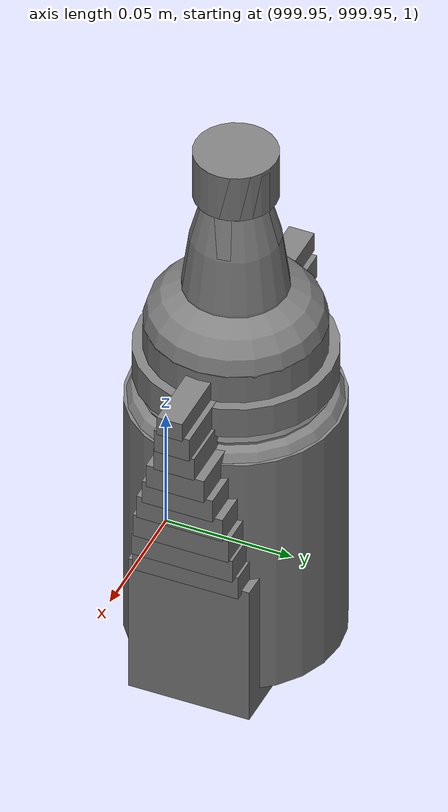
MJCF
<mujoco>
    <option gravity="0.000000000 0.000000000 -9.810000420" timestep="0.0166666" integrator="implicitfast" density="1.225" viscosity="1.8000001e-05" noslip_iterations="10" iterations="100" sdf_iterations="50">
        <flag multiccd="disable"/>
    </option>
    <size memory="1000M"/>
    <compiler coordinate="local"/>
    <worldbody>
        <light cutoff="30" pos="0 1 1" dir="0 -1 -2"/>
        <light cutoff="30" pos="0 -1 1" dir="0 1 -2"/>
        <body pos="0.000000000 0.000000000 0.000000000" euler="0.000000000 0.000000000 0.000000000" name="Interactive Objects_Interactive Objects"/>
        <body pos="1000.000000000 1000.000000000 1.000000000" euler="0.000000000 0.000000000 0.000000000" name="openloong_gripper_2f85_fix_base_usda_bottle_blue">
            <geom contype="1" conaffinity="1" density="1000" type="ellipsoid" material="" rgba="0.500000000 0.500000000 0.500000000 1.000000000" solimp="0.899999976 0.949999988 0.001000000" friction="1.000000000 0.005000000 0.000100000" solref="0.020000000 1.000000000" margin="0" condim="3" group="0" pos="0.000000000 0.000000000 0.118920922" quat="1.000000000 0.000000000 0.000000000 0.000000000" size="0.030999999 0.030999999 0.029999999" name="openloong_gripper_2f85_fix_base_usda_geom_E528AF93_6D74_4731_AD7C_3B1B1E3A1AE3"/>
            <geom contype="1" conaffinity="1" density="1000" type="box" material="" rgba="0.500000000 0.500000000 0.500000000 1.000000000" solimp="0.899999976 0.949999988 0.001000000" friction="1.000000000 0.005000000 0.000100000" solref="0.020000000 1.000000000" margin="0" condim="3" group="0" pos="0.000000000 0.000000000 0.002164602" quat="1.000000000 0.000000000 0.000000000 0.000000000" size="0.020000000 0.020000000 0.003000000" name="openloong_gripper_2f85_fix_base_usda_geom_27CCEE94_EDF5_4BCB_9854_41F285253C14"/>
            <geom contype="1" conaffinity="1" density="1000" type="cylinder" material="" rgba="0.500000000 0.500000000 0.500000000 1.000000000" solimp="0.899999976 0.949999988 0.001000000" friction="1.000000000 0.005000000 0.000100000" solref="0.020000000 1.000000000" margin="0" condim="3" group="0" pos="0.000000000 -0.000366211 0.060859680" quat="1.000000000 0.000000000 0.000000000 0.000000000" size="0.030999999 0.057999998 1.000000000" name="openloong_gripper_2f85_fix_base_usda_geom_349A0632_9EDC_4E38_ABA7_0F77EB8634FA"/>
            <geom contype="1" conaffinity="1" density="1000" type="cylinder" material="" rgba="0.500000000 0.500000000 0.500000000 1.000000000" solimp="0.899999976 0.949999988 0.001000000" friction="1.000000000 0.005000000 0.000100000" solref="0.020000000 1.000000000" margin="0" condim="3" group="0" pos="0.000000000 0.000000000 0.220594406" quat="1.000000000 0.000000000 0.000000000 0.000000000" size="0.016000001 0.010000000 1.000000000" name="openloong_gripper_2f85_fix_base_usda_geom_ED8EBDA7_A321_43B8_994C_D1E21F91692B"/>
            <geom contype="1" conaffinity="1" density="1000" type="ellipsoid" material="" rgba="0.500000000 0.500000000 0.500000000 1.000000000" solimp="0.899999976 0.949999988 0.001000000" friction="1.000000000 0.005000000 0.000100000" solref="0.020000000 1.000000000" margin="0" condim="3" group="0" pos="0.000000000 0.000000000 0.144259930" quat="1.000000000 0.000000000 0.000000000 0.000000000" size="0.021000000 0.021000000 0.079999998" name="openloong_gripper_2f85_fix_base_usda_geom_B0D06BF1_12DA_475C_89F0_88891E292C9F"/>
            <freejoint name="openloong_gripper_2f85_fix_base_usda_bottle_blue_joint"/>
            <site size="0.005000000 0.005000000 0.005000000" rgba="0.500000000 0.500000000 0.500000000 1.000000000" pos="0.000000000 0.000000000 0.000000000" quat="0.999961913 0.008726535 0.000000000 0.000000000" group="0" type="sphere" name="openloong_gripper_2f85_fix_base_usda_bottle_bluesite"/>
        </body>
        <body pos="1000.000000000 1000.000000000 1.000000000" euler="0.000000000 0.000000000 0.000000000" name="openloong_gripper_2f85_fix_base_usda_salt">
            <geom contype="1" conaffinity="1" density="1000" type="box" material="" rgba="0.500000000 0.500000000 0.500000000 1.000000000" solimp="0.899999976 0.949999988 0.001000000" friction="1.000000000 0.005000000 0.000100000" solref="0.020000000 1.000000000" margin="0" condim="3" group="0" pos="0.000305176 0.000000000 0.084862232" quat="1.000000000 0.000000000 0.000000000 0.000000000" size="0.048999999 0.018999999 0.005000000" name="openloong_gripper_2f85_fix_base_usda_geom_B1BE1A6B_8284_4167_9459_0609FCB567EF"/>
            <geom contype="1" conaffinity="1" density="1000" type="box" material="" rgba="0.500000000 0.500000000 0.500000000 1.000000000" solimp="0.899999976 0.949999988 0.001000000" friction="1.000000000 0.005000000 0.000100000" solref="0.020000000 1.000000000" margin="0" condim="3" group="0" pos="0.000305176 0.000000000 0.104564309" quat="1.000000000 0.000000000 0.000000000 0.000000000" size="0.052000001 0.014000000 0.005000000" name="openloong_gripper_2f85_fix_base_usda_geom_1EB995F9_62CB_4582_9A81_BE558A75512D"/>
            <geom contype="1" conaffinity="1" density="1000" type="box" material="" rgba="0.500000000 0.500000000 0.500000000 1.000000000" solimp="0.899999976 0.949999988 0.001000000" friction="1.000000000 0.005000000 0.000100000" solref="0.020000000 1.000000000" margin="0" condim="3" group="0" pos="0.000305176 0.000000000 0.114487171" quat="1.000000000 0.000000000 0.000000000 0.000000000" size="0.054000001 0.011500000 0.005000000" name="openloong_gripper_2f85_fix_base_usda_geom_4ADB57D6_BCA0_4C00_88B7_82BC2E352BA7"/>
            <geom contype="1" conaffinity="1" density="1000" type="box" material="" rgba="0.500000000 0.500000000 0.500000000 1.000000000" solimp="0.899999976 0.949999988 0.001000000" friction="1.000000000 0.005000000 0.000100000" solref="0.020000000 1.000000000" margin="0" condim="3" group="0" pos="0.000305176 0.000000000 0.075103164" quat="1.000000000 0.000000000 0.000000000 0.000000000" size="0.048000000 0.020000000 0.005000000" name="openloong_gripper_2f85_fix_base_usda_geom_DCDDBC36_2AD3_45D5_A571_45480C322656"/>
            <geom contype="1" conaffinity="1" density="1000" type="box" material="" rgba="0.500000000 0.500000000 0.500000000 1.000000000" solimp="0.899999976 0.949999988 0.001000000" friction="1.000000000 0.005000000 0.000100000" solref="0.020000000 1.000000000" margin="0" condim="3" group="0" pos="0.000305176 0.000000000 0.134892464" quat="1.000000000 0.000000000 0.000000000 0.000000000" size="0.057000000 0.007000000 0.005000000" name="openloong_gripper_2f85_fix_base_usda_geom_CACF61DC_B910_482F_98F6_EE0122A1D747"/>
            <geom contype="1" conaffinity="1" density="1000" type="box" material="" rgba="0.500000000 0.500000000 0.500000000 1.000000000" solimp="0.899999976 0.949999988 0.001000000" friction="1.000000000 0.005000000 0.000100000" solref="0.020000000 1.000000000" margin="0" condim="3" group="0" pos="0.000305176 0.000000000 0.094920278" quat="1.000000000 0.000000000 0.000000000 0.000000000" size="0.050000001 0.017000001 0.005000000" name="openloong_gripper_2f85_fix_base_usda_geom_E7E08812_9EED_4149_BB78_F3D2F0D2F303"/>
            <geom contype="1" conaffinity="1" density="1000" type="box" material="" rgba="0.500000000 0.500000000 0.500000000 1.000000000" solimp="0.899999976 0.949999988 0.001000000" friction="1.000000000 0.005000000 0.000100000" solref="0.020000000 1.000000000" margin="0" condim="3" group="0" pos="0.000305176 0.000000000 0.065204859" quat="1.000000000 0.000000000 0.000000000 0.000000000" size="0.045000002 0.021000000 0.005000000" name="openloong_gripper_2f85_fix_base_usda_geom_6B6A0F38_72EC_47DC_8B68_5E6AF7E42D61"/>
            <geom contype="1" conaffinity="1" density="1000" type="box" material="" rgba="0.500000000 0.500000000 0.500000000 1.000000000" solimp="0.899999976 0.949999988 0.001000000" friction="1.000000000 0.005000000 0.000100000" solref="0.020000000 1.000000000" margin="0" condim="3" group="0" pos="0.000305176 0.000000000 0.144135714" quat="1.000000000 0.000000000 0.000000000 0.000000000" size="0.059000000 0.005000000 0.004000000" name="openloong_gripper_2f85_fix_base_usda_geom_C3C02FFE_9DE6_463A_8D56_93BA44F08EC2"/>
            <geom contype="1" conaffinity="1" density="1000" type="box" material="" rgba="0.500000000 0.500000000 0.500000000 1.000000000" solimp="0.899999976 0.949999988 0.001000000" friction="1.000000000 0.005000000 0.000100000" solref="0.020000000 1.000000000" margin="0" condim="3" group="0" pos="0.000000000 0.000000000 0.031593561" quat="1.000000000 0.000000000 0.000000000 0.000000000" size="0.041999999 0.024000000 0.029999999" name="openloong_gripper_2f85_fix_base_usda_geom_44EA661A_0EB3_4161_B846_B1D0B7CF8F08"/>
            <geom contype="1" conaffinity="1" density="1000" type="box" material="" rgba="0.500000000 0.500000000 0.500000000 1.000000000" solimp="0.899999976 0.949999988 0.001000000" friction="1.000000000 0.005000000 0.000100000" solref="0.020000000 1.000000000" margin="0" condim="3" group="0" pos="0.000305176 0.000000000 0.124608755" quat="1.000000000 0.000000000 0.000000000 0.000000000" size="0.055000000 0.008000000 0.005000000" name="openloong_gripper_2f85_fix_base_usda_geom_A623A3BD_BE51_418A_A52B_6B6A0F0DE74D"/>
            <freejoint name="openloong_gripper_2f85_fix_base_usda_salt_joint"/>
            <site size="0.005000000 0.005000000 0.005000000" rgba="0.500000000 0.500000000 0.500000000 1.000000000" pos="0.000000000 0.000000000 0.000000000" quat="1.000000000 0.000000000 0.000000000 0.000000000" group="0" type="sphere" name="openloong_gripper_2f85_fix_base_usda_saltsite"/>
        </body>
        <body pos="1000.000000000 1000.000000000 1.000000000" euler="0.000000000 0.000000000 0.000000000" name="openloong_gripper_2f85_fix_base_usda_can">
            <geom contype="1" conaffinity="1" density="1000" type="cylinder" material="" rgba="0.500000000 0.500000000 0.500000000 1.000000000" solimp="0.899999976 0.949999988 0.001000000" friction="1.000000000 0.005000000 0.000100000" solref="0.020000000 1.000000000" margin="0" condim="3" group="0" pos="0.000000000 0.000000000 0.079676986" quat="1.000000000 0.000000000 0.000000000 0.000000000" size="0.034000002 0.071999997 1.000000000" name="openloong_gripper_2f85_fix_base_usda_geom_6E847ADA_C7ED_458D_9823_83C12C0EB5D0"/>
            <geom contype="1" conaffinity="1" density="1000" type="ellipsoid" material="" rgba="0.500000000 0.500000000 0.500000000 1.000000000" solimp="0.899999976 0.949999988 0.001000000" friction="1.000000000 0.005000000 0.000100000" solref="0.020000000 1.000000000" margin="0" condim="3" group="0" pos="0.000000000 0.000000000 0.151854277" quat="1.000000000 0.000000000 0.000000000 0.000000000" size="0.034000002 0.034000002 0.020000000" name="openloong_gripper_2f85_fix_base_usda_geom_6D5E4504_4F37_4EFE_995E_5BA3B889B69B"/>
            <geom contype="1" conaffinity="1" density="1000" type="box" material="" rgba="0.500000000 0.500000000 0.500000000 1.000000000" solimp="0.899999976 0.949999988 0.001000000" friction="1.000000000 0.005000000 0.000100000" solref="0.020000000 1.000000000" margin="0" condim="3" group="0" pos="0.000000000 0.000000000 0.004777670" quat="1.000000000 0.000000000 0.000000000 0.000000000" size="0.020000000 0.020000000 0.005000000" name="openloong_gripper_2f85_fix_base_usda_geom_D6AEE98E_E824_4248_8716_6B39B1D9665C"/>
            <freejoint name="openloong_gripper_2f85_fix_base_usda_can_joint"/>
            <site size="0.005000000 0.005000000 0.005000000" rgba="0.500000000 0.500000000 0.500000000 1.000000000" pos="0.000000000 0.000000000 0.000000000" quat="1.000000000 0.000000000 0.000000000 0.000000000" group="0" type="sphere" name="openloong_gripper_2f85_fix_base_usda_cansite"/>
        </body>
        <body pos="1000.000000000 1000.000000000 1.000000000" euler="0.000000000 0.000000000 0.000000000" name="openloong_gripper_2f85_fix_base_usda_bottle_red">
            <geom contype="1" conaffinity="1" density="1000" type="ellipsoid" material="" rgba="0.500000000 0.500000000 0.500000000 1.000000000" solimp="0.899999976 0.949999988 0.001000000" friction="1.000000000 0.005000000 0.000100000" solref="0.020000000 1.000000000" margin="0" condim="3" group="0" pos="0.000000000 0.000000000 0.144284487" quat="1.000000000 0.000000000 0.000000000 0.000000000" size="0.021000000 0.021000000 0.079999998" name="openloong_gripper_2f85_fix_base_usda_geom_5AA853C1_960D_4341_80D4_CA7504C2FCE0"/>
            <geom contype="1" conaffinity="1" density="1000" type="cylinder" material="" rgba="0.500000000 0.500000000 0.500000000 1.000000000" solimp="0.899999976 0.949999988 0.001000000" friction="1.000000000 0.005000000 0.000100000" solref="0.020000000 1.000000000" margin="0" condim="3" group="0" pos="0.000000000 0.000000000 0.220618963" quat="1.000000000 0.000000000 0.000000000 0.000000000" size="0.016000001 0.010000000 1.000000000" name="openloong_gripper_2f85_fix_base_usda_geom_EF24D90B_F889_4DBF_B1BB_F88F617B6F57"/>
            <geom contype="1" conaffinity="1" density="1000" type="ellipsoid" material="" rgba="0.500000000 0.500000000 0.500000000 1.000000000" solimp="0.899999976 0.949999988 0.001000000" friction="1.000000000 0.005000000 0.000100000" solref="0.020000000 1.000000000" margin="0" condim="3" group="0" pos="0.000000000 0.000000000 0.118945479" quat="1.000000000 0.000000000 0.000000000 0.000000000" size="0.030999999 0.030999999 0.029999999" name="openloong_gripper_2f85_fix_base_usda_geom_6221D512_91E5_454E_962D_A51C9959B5A4"/>
            <geom contype="1" conaffinity="1" density="1000" type="box" material="" rgba="0.500000000 0.500000000 0.500000000 1.000000000" solimp="0.899999976 0.949999988 0.001000000" friction="1.000000000 0.005000000 0.000100000" solref="0.020000000 1.000000000" margin="0" condim="3" group="0" pos="0.000000000 0.000000000 0.002189159" quat="1.000000000 0.000000000 0.000000000 0.000000000" size="0.020000000 0.020000000 0.003000000" name="openloong_gripper_2f85_fix_base_usda_geom_D4F47549_5D3A_4774_A7D9_F0C4944D7E88"/>
            <geom contype="1" conaffinity="1" density="1000" type="cylinder" material="" rgba="0.500000000 0.500000000 0.500000000 1.000000000" solimp="0.899999976 0.949999988 0.001000000" friction="1.000000000 0.005000000 0.000100000" solref="0.020000000 1.000000000" margin="0" condim="3" group="0" pos="0.000000000 -0.000366211 0.060884237" quat="1.000000000 0.000000000 0.000000000 0.000000000" size="0.030999999 0.057999998 1.000000000" name="openloong_gripper_2f85_fix_base_usda_geom_D30D6393_EFC7_4BE6_817C_5F433CD31E13"/>
            <freejoint name="openloong_gripper_2f85_fix_base_usda_bottle_red_joint"/>
            <site size="0.005000000 0.005000000 0.005000000" rgba="0.500000000 0.500000000 0.500000000 1.000000000" pos="0.000000000 0.000000000 0.000000000" quat="0.999961913 0.008726535 0.000000000 0.000000000" group="0" type="sphere" name="openloong_gripper_2f85_fix_base_usda_bottle_redsite"/>
        </body>
        <body pos="-2.319067717 5.762400150 1.844595671" euler="-168.226119995 9.113678932 111.783889771" mocap="true" name="spotlight1_SpotLight"/>
        <body pos="1000.000000000 1000.000000000 1.000000000" euler="0.000000000 0.000000000 0.000000000" name="openloong_gripper_2f85_fix_base_usda_jar_01">
            <geom contype="1" conaffinity="1" density="1000" type="box" material="" rgba="0.500000000 0.500000000 0.500000000 1.000000000" solimp="0.899999976 0.949999988 0.001000000" friction="1.000000000 0.005000000 0.000100000" solref="0.020000000 1.000000000" margin="0" condim="3" group="0" pos="0.000000000 0.000000000 0.006158113" quat="1.000000000 0.000000000 0.000000000 0.000000000" size="0.020000000 0.020000000 0.005000000" name="openloong_gripper_2f85_fix_base_usda_geom_8DC74FE9_C019_4F49_88FD_70C8422610DA"/>
            <geom contype="1" conaffinity="1" density="1000" type="cylinder" material="" rgba="0.500000000 0.500000000 0.500000000 1.000000000" solimp="0.899999976 0.949999988 0.001000000" friction="1.000000000 0.005000000 0.000100000" solref="0.020000000 1.000000000" margin="0" condim="3" group="0" pos="0.000000000 0.000000000 0.062744498" quat="1.000000000 0.000000000 0.000000000 0.000000000" size="0.041000001 0.052999999 1.000000000" name="openloong_gripper_2f85_fix_base_usda_geom_34180A2D_9C84_4D67_BA62_A44912127D0F"/>
            <geom contype="1" conaffinity="1" density="1000" type="ellipsoid" material="" rgba="0.500000000 0.500000000 0.500000000 1.000000000" solimp="0.899999976 0.949999988 0.001000000" friction="1.000000000 0.005000000 0.000100000" solref="0.020000000 1.000000000" margin="0" condim="3" group="0" pos="0.000000000 0.000000000 0.122252703" quat="1.000000000 0.000000000 0.000000000 0.000000000" size="0.035999998 0.035999998 0.010000000" name="openloong_gripper_2f85_fix_base_usda_geom_E592D549_01CB_489E_83D6_ED5E96657561"/>
            <geom contype="1" conaffinity="1" density="1000" type="cylinder" material="" rgba="0.500000000 0.500000000 0.500000000 1.000000000" solimp="0.899999976 0.949999988 0.001000000" friction="1.000000000 0.005000000 0.000100000" solref="0.020000000 1.000000000" margin="0" condim="3" group="0" pos="0.000000000 0.000000000 0.015747190" quat="1.000000000 0.000000000 0.000000000 0.000000000" size="0.035000000 0.010000000 1.000000000" name="openloong_gripper_2f85_fix_base_usda_geom_D6E04D82_E70B_42AB_BCFA_8B71B4162748"/>
            <geom contype="1" conaffinity="1" density="1000" type="ellipsoid" material="" rgba="0.500000000 0.500000000 0.500000000 1.000000000" solimp="0.899999976 0.949999988 0.001000000" friction="1.000000000 0.005000000 0.000100000" solref="0.020000000 1.000000000" margin="0" condim="3" group="0" pos="0.000000000 0.000000000 0.115815401" quat="1.000000000 0.000000000 0.000000000 0.000000000" size="0.039999999 0.039999999 0.010000000" name="openloong_gripper_2f85_fix_base_usda_geom_14794DE4_1CB9_4536_9D48_A5B61F5CBE92"/>
            <geom contype="1" conaffinity="1" density="1000" type="cylinder" material="" rgba="0.500000000 0.500000000 0.500000000 1.000000000" solimp="0.899999976 0.949999988 0.001000000" friction="1.000000000 0.005000000 0.000100000" solref="0.020000000 1.000000000" margin="0" condim="3" group="0" pos="0.000000000 0.000000000 0.133183479" quat="1.000000000 0.000000000 0.000000000 0.000000000" size="0.037999999 0.006500000 1.000000000" name="openloong_gripper_2f85_fix_base_usda_geom_87A57677_DC19_46E2_A786_44385941EA40"/>
            <freejoint name="openloong_gripper_2f85_fix_base_usda_jar_01_joint"/>
            <site size="0.005000000 0.005000000 0.005000000" rgba="0.500000000 0.500000000 0.500000000 1.000000000" pos="0.000000000 0.000000000 0.000000000" quat="1.000000000 0.000000000 0.000000000 0.000000000" group="0" type="sphere" name="openloong_gripper_2f85_fix_base_usda_jar_01site"/>
        </body>
        <body pos="-2.104979038 6.402857304 1.681154728" euler="-132.176879883 80.936767578 119.826782227" mocap="true" name="spotlight3_SpotLight"/>
        <body pos="-2.324707985 6.169364452 1.857098937" euler="110.251617432 88.970802307 154.839172363" mocap="true" name="spotlight4_SpotLight"/>
        <body pos="0.000000000 0.000000000 0.000000000" euler="0.000000000 0.000000000 0.000000000" name=" Static Objects_ Static Objects">
            <geom contype="1" conaffinity="1" density="1000" type="box" material="" rgba="0.500000000 0.500000000 0.500000000 1.000000000" solimp="0.899999976 0.949999988 0.001000000" friction="1.000000000 0.005000000 0.000100000" solref="0.020000000 1.000000000" margin="0" condim="3" group="0" pos="-6.286010742 6.153595448 1.563861728" quat="0.707107067 0.000000000 0.000000000 0.707106471" size="0.529999971 3.134999990 0.025000000" name=" Static Objects_geom_295041FB_15A2_4C7C_9ACB_CEADAFC16D58"/>
            <geom contype="1" conaffinity="1" density="1000" type="box" material="" rgba="0.500000000 0.500000000 0.500000000 1.000000000" solimp="0.899999976 0.949999988 0.001000000" friction="1.000000000 0.005000000 0.000100000" solref="0.020000000 1.000000000" margin="0" condim="3" group="0" pos="-3.101639986 6.150595188 1.018643856" quat="1.000000000 0.000000000 0.000000000 0.000000000" size="0.050000001 0.579999983 1.019999981" name=" Static Objects_geom_A23D08AE_250E_46ED_BBD0_13607E20E3E3"/>
            <geom contype="1" conaffinity="1" density="1000" type="box" material="" rgba="0.500000000 0.500000000 0.500000000 1.000000000" solimp="0.899999976 0.949999988 0.001000000" friction="1.000000000 0.005000000 0.000100000" solref="0.020000000 1.000000000" margin="0" condim="3" group="0" pos="-2.825197220 6.153595448 1.563861728" quat="0.707107067 0.000000000 0.000000000 0.707106471" size="0.550000012 0.239999995 0.025000000" name=" Static Objects_geom_C03B3054_F5E7_425E_92E5_5239305E92AD"/>
            <geom contype="1" conaffinity="1" density="1000" type="box" material="" rgba="0.500000000 0.500000000 0.500000000 1.000000000" solimp="0.899999976 0.949999988 0.001000000" friction="1.000000000 0.005000000 0.000100000" solref="0.020000000 1.000000000" margin="0" condim="3" group="0" pos="-6.311686516 6.153595448 1.018643856" quat="0.707107067 0.000000000 0.000000000 0.707106471" size="0.050000001 3.150000095 1.019999981" name=" Static Objects_geom_D4E1FE1B_D15E_4639_98B3_743E9D7A92FF"/>
            <geom contype="1" conaffinity="1" density="1000" type="box" material="" rgba="0.500000000 0.500000000 0.500000000 1.000000000" solimp="0.899999976 0.949999988 0.001000000" friction="1.000000000 0.005000000 0.000100000" solref="0.020000000 1.000000000" margin="0" condim="3" group="0" pos="-2.825197220 6.153595448 1.115278244" quat="0.707107067 0.000000000 0.000000000 0.707106471" size="0.550000012 0.239999995 0.025000000" name=" Static Objects_geom_D054AFA4_C94D_43E0_A85F_138C21585AC1"/>
            <geom contype="1" conaffinity="1" density="1000" type="box" material="" rgba="0.500000000 0.500000000 0.500000000 1.000000000" solimp="0.899999976 0.949999988 0.001000000" friction="1.000000000 0.005000000 0.000100000" solref="0.020000000 1.000000000" margin="0" condim="3" group="0" pos="-6.293097973 6.153595448 1.114443064" quat="0.707107067 0.000000000 0.000000000 0.707106471" size="0.529999971 3.134999990 0.025000000" name=" Static Objects_geom_031AF778_0D40_4F13_ACC2_11B729731AAC"/>
            <geom contype="1" conaffinity="1" density="1000" type="box" material="" rgba="0.500000000 0.500000000 0.500000000 1.000000000" solimp="0.899999976 0.949999988 0.001000000" friction="1.000000000 0.005000000 0.000100000" solref="0.020000000 1.000000000" margin="0" condim="3" group="0" pos="-2.825197220 6.153595448 0.629031777" quat="0.707107067 0.000000000 0.000000000 0.707106471" size="0.550000012 0.239999995 0.025000000" name=" Static Objects_geom_A0A9FECF_DB1B_4BE4_89CC_3C3373A00C22"/>
            <geom contype="1" conaffinity="1" density="1000" type="box" material="" rgba="0.500000000 0.500000000 0.500000000 1.000000000" solimp="0.899999976 0.949999988 0.001000000" friction="1.000000000 0.005000000 0.000100000" solref="0.020000000 1.000000000" margin="0" condim="3" group="0" pos="-6.286010742 6.153595448 0.096129179" quat="0.707107067 0.000000000 0.000000000 0.707106471" size="0.529999971 3.134999990 0.098999999" name=" Static Objects_geom_9050BDE4_1238_4C90_9B2B_DCB75DEDD431"/>
            <geom contype="1" conaffinity="1" density="1000" type="box" material="" rgba="0.500000000 0.500000000 0.500000000 1.000000000" solimp="0.899999976 0.949999988 0.001000000" friction="1.000000000 0.005000000 0.000100000" solref="0.020000000 1.000000000" margin="0" condim="3" group="0" pos="-2.825197220 6.153595448 0.097434282" quat="0.707107067 0.000000000 0.000000000 0.707106471" size="0.550000012 0.239999995 0.098999999" name=" Static Objects_geom_41CAA496_F18B_43C5_BA36_1067F1F97DE0"/>
            <geom contype="1" conaffinity="1" density="1000" type="box" material="" rgba="0.500000000 0.500000000 0.500000000 1.000000000" solimp="0.899999976 0.949999988 0.001000000" friction="1.000000000 0.005000000 0.000100000" solref="0.020000000 1.000000000" margin="0" condim="3" group="0" pos="-6.286010742 6.153595448 0.629031777" quat="0.707107067 0.000000000 0.000000000 0.707106471" size="0.529999971 3.134999990 0.025000000" name=" Static Objects_geom_C719CB76_B0B4_4826_96D1_8592E610C43E"/>
            <geom contype="1" conaffinity="1" density="1000" type="box" material="" rgba="0.500000000 0.500000000 0.500000000 1.000000000" solimp="0.899999976 0.949999988 0.001000000" friction="1.000000000 0.005000000 0.000100000" solref="0.020000000 1.000000000" margin="0" condim="3" group="0" pos="-6.000000000 20.159999847 2.000000000" quat="1.000000000 0.000000000 0.000000000 0.000000000" size="6.079999924 0.070000000 2.000000000" name=" Static Objects_geom_EEA640A0_236F_4911_9DCD_A2B3070046BC"/>
            <geom contype="1" conaffinity="1" density="1000" type="box" material="" rgba="0.500000000 0.500000000 0.500000000 1.000000000" solimp="0.899999976 0.949999988 0.001000000" friction="1.000000000 0.005000000 0.000100000" solref="0.020000000 1.000000000" margin="0" condim="3" group="0" pos="-6.000000000 0.035000000 2.000000000" quat="1.000000000 0.000000000 0.000000000 0.000000000" size="6.079999924 0.070000000 2.000000000" name=" Static Objects_geom_88123743_92A1_458F_85CD_69583D166E86"/>
            <geom contype="1" conaffinity="1" density="1000" type="box" material="" rgba="0.500000000 0.500000000 0.500000000 1.000000000" solimp="0.899999976 0.949999988 0.001000000" friction="1.000000000 0.005000000 0.000100000" solref="0.020000000 1.000000000" margin="0" condim="3" group="0" pos="0.000000000 10.000000000 2.000000000" quat="1.000000000 0.000000000 0.000000000 0.000000000" size="0.070000000 10.500000000 2.000000000" name=" Static Objects_geom_D67342A3_96C4_4DD8_BC59_F72A02077967"/>
            <geom contype="1" conaffinity="1" density="1000" type="box" material="" rgba="0.500000000 0.500000000 0.500000000 1.000000000" solimp="0.899999976 0.949999988 0.001000000" friction="1.000000000 0.005000000 0.000100000" solref="0.020000000 1.000000000" margin="0" condim="3" group="0" pos="-12.050000191 10.000000000 2.000000000" quat="1.000000000 0.000000000 0.000000000 0.000000000" size="0.070000000 10.500000000 2.000000000" name=" Static Objects_geom_B8178D96_826C_4639_B9BF_23CB1A390D55"/>
            <geom contype="1" conaffinity="1" density="1000" type="plane" material="" rgba="0.500000000 0.500000000 0.500000000 1.000000000" solimp="0.899999976 0.949999988 0.001000000" friction="1.000000000 0.005000000 0.000100000" solref="0.020000000 1.000000000" margin="0" condim="3" group="0" pos="-6.000000000 10.399999619 0.000000000" quat="1.000000000 0.000000000 0.000000000 0.000000000" size="6.050000191 10.800000191 0.010000000" name=" Static Objects_geom_081F5BB8_70A8_42ED_A39E_7EC121FDA069"/>
            <geom contype="1" conaffinity="1" density="1000" type="box" material="" rgba="0.500000000 0.500000000 0.500000000 1.000000000" solimp="0.899999976 0.949999988 0.001000000" friction="1.000000000 0.005000000 0.000100000" solref="0.020000000 1.000000000" margin="0" condim="3" group="0" pos="-8.830721855 2.096410990 0.549305558" quat="1.000000000 0.000000000 0.000000000 0.000000000" size="0.280000001 0.430000007 0.550000012" name=" Static Objects_geom_E60CA5D4_E23F_485D_A2BD_A200050E8C76"/>
            <geom contype="1" conaffinity="1" density="1000" type="box" material="" rgba="0.500000000 0.500000000 0.500000000 1.000000000" solimp="0.899999976 0.949999988 0.001000000" friction="1.000000000 0.005000000 0.000100000" solref="0.020000000 1.000000000" margin="0" condim="3" group="0" pos="-6.460197449 2.937205315 0.548931718" quat="1.000000000 0.000000000 0.000000000 0.000000000" size="2.650000095 0.430000007 0.550000012" name=" Static Objects_geom_18B3A4C2_353B_49B4_968F_A7A0A25110C9"/>
            <geom contype="1" conaffinity="1" density="1000" type="box" material="" rgba="0.500000000 0.500000000 0.500000000 1.000000000" solimp="0.899999976 0.949999988 0.001000000" friction="1.000000000 0.005000000 0.000100000" solref="0.020000000 1.000000000" margin="0" condim="3" group="0" pos="-4.240264893 1.327049494 0.549888909" quat="1.000000000 0.000000000 0.000000000 0.000000000" size="0.430000007 1.200000048 0.550000012" name=" Static Objects_geom_41BF9829_9309_4B94_8632_DC5218686BE5"/>
            <geom contype="1" conaffinity="1" density="1000" type="box" material="" rgba="0.500000000 0.500000000 0.500000000 1.000000000" solimp="0.899999976 0.949999988 0.001000000" friction="1.000000000 0.005000000 0.000100000" solref="0.020000000 1.000000000" margin="0" condim="3" group="0" pos="-7.408766270 3.088089943 1.776644945" quat="0.928051054 0.000000000 0.000000000 0.372453064" size="0.050000001 0.100000001 0.050000001" name=" Static Objects_geom_D0BC34B7_D140_415C_A0C8_4393AA7C3EB6"/>
            <geom contype="1" conaffinity="1" density="1000" type="box" material="" rgba="0.500000000 0.500000000 0.500000000 1.000000000" solimp="0.899999976 0.949999988 0.001000000" friction="1.000000000 0.005000000 0.000100000" solref="0.020000000 1.000000000" margin="0" condim="3" group="0" pos="-7.437745571 3.067511320 1.289965630" quat="1.000000000 0.000000000 0.000000000 0.000000000" size="0.029999999 0.020000000 0.020000000" name=" Static Objects_geom_53F90668_C9AB_4EFE_9D1F_1BF8C757E67A"/>
            <geom contype="1" conaffinity="1" density="1000" type="box" material="" rgba="0.500000000 0.500000000 0.500000000 1.000000000" solimp="0.899999976 0.949999988 0.001000000" friction="1.000000000 0.005000000 0.000100000" solref="0.020000000 1.000000000" margin="0" condim="3" group="0" pos="-7.719123363 2.867671013 1.173410416" quat="1.000000000 0.000000000 0.000000000 0.000000000" size="0.250000000 0.250000000 0.079999998" name=" Static Objects_geom_0594EDFB_A794_4DB6_BEBF_8D3FB99619DD"/>
            <geom contype="1" conaffinity="1" density="1000" type="box" material="" rgba="0.500000000 0.500000000 0.500000000 1.000000000" solimp="0.899999976 0.949999988 0.001000000" friction="1.000000000 0.005000000 0.000100000" solref="0.020000000 1.000000000" margin="0" condim="3" group="0" pos="-7.719123363 2.958004713 1.530241251" quat="1.000000000 0.000000000 0.000000000 0.000000000" size="0.250000000 0.159999996 0.280000001" name=" Static Objects_geom_2114DAEB_BB48_4DED_9099_83F66798DB9C"/>
            <geom contype="1" conaffinity="1" density="1000" type="cylinder" material="" rgba="0.500000000 0.500000000 0.500000000 1.000000000" solimp="0.899999976 0.949999988 0.001000000" friction="1.000000000 0.005000000 0.000100000" solref="0.020000000 1.000000000" margin="0" condim="3" group="0" pos="-7.427312374 3.069516420 1.502544641" quat="0.928051054 0.000000000 0.000000000 0.372453064" size="0.015000000 0.230000004 0.100000001" name=" Static Objects_geom_41984C4E_3F60_49DB_98B8_1D2C759ECF51"/>
            <geom contype="1" conaffinity="1" density="1000" type="box" material="" rgba="0.500000000 0.500000000 0.500000000 1.000000000" solimp="0.899999976 0.949999988 0.001000000" friction="1.000000000 0.005000000 0.000100000" solref="0.020000000 1.000000000" margin="0" condim="3" group="0" pos="-9.058088303 6.434794426 1.209077358" quat="1.000000000 0.000000000 0.000000000 0.000000000" size="0.250000000 0.100000001 0.070000000" name=" Static Objects_geom_B24E0EE4_4BE0_4D22_9618_9AB31AB16B06"/>
            <geom contype="1" conaffinity="1" density="1000" type="box" material="" rgba="0.500000000 0.500000000 0.500000000 1.000000000" solimp="0.899999976 0.949999988 0.001000000" friction="1.000000000 0.005000000 0.000100000" solref="0.020000000 1.000000000" margin="0" condim="3" group="0" pos="-5.611940861 6.318420410 0.350975692" quat="1.000000000 0.000000000 0.000000000 0.000000000" size="0.699999988 0.100000001 0.150000006" name=" Static Objects_geom_3813A948_D090_4D70_803E_31B8BE9B57EC"/>
            <geom contype="1" conaffinity="1" density="1000" type="box" material="" rgba="0.500000000 0.500000000 0.500000000 1.000000000" solimp="0.899999976 0.949999988 0.001000000" friction="1.000000000 0.005000000 0.000100000" solref="0.020000000 1.000000000" margin="0" condim="3" group="0" pos="-9.237723351 6.464855671 1.209077358" quat="1.000000000 0.000000000 0.000000000 0.000000000" size="0.100000001 0.100000001 0.070000000" name=" Static Objects_geom_204F7BE9_8ADB_42C8_9FF1_7B4F40BA285E"/>
            <geom contype="1" conaffinity="1" density="1000" type="box" material="" rgba="0.500000000 0.500000000 0.500000000 1.000000000" solimp="0.899999976 0.949999988 0.001000000" friction="1.000000000 0.005000000 0.000100000" solref="0.020000000 1.000000000" margin="0" condim="3" group="0" pos="-6.300771236 6.459744930 1.744376063" quat="1.000000000 0.000000000 0.000000000 0.000000000" size="3.000000000 0.200000003 0.150000006" name=" Static Objects_geom_81621079_71A0_44FF_B0A6_0E45DC7119B8"/>
            <geom contype="1" conaffinity="1" density="1000" type="box" material="" rgba="0.500000000 0.500000000 0.500000000 1.000000000" solimp="0.899999976 0.949999988 0.001000000" friction="1.000000000 0.005000000 0.000100000" solref="0.020000000 1.000000000" margin="0" condim="3" group="0" pos="-7.373087406 6.458900928 1.214329123" quat="1.000000000 0.000000000 0.000000000 0.000000000" size="0.250000000 0.200000003 0.075000003" name=" Static Objects_geom_2F0BBAA0_8F92_4DA8_B253_61EA6BE4D48C"/>
            <geom contype="1" conaffinity="1" density="1000" type="box" material="" rgba="0.500000000 0.500000000 0.500000000 1.000000000" solimp="0.899999976 0.949999988 0.001000000" friction="1.000000000 0.005000000 0.000100000" solref="0.020000000 1.000000000" margin="0" condim="3" group="0" pos="-4.035642624 6.459744930 0.352518857" quat="1.000000000 0.000000000 0.000000000 0.000000000" size="0.800000012 0.200000003 0.150000006" name=" Static Objects_geom_D02A3B22_DC20_451B_9371_2BD2F4040FDA"/>
            <geom contype="1" conaffinity="1" density="1000" type="box" material="" rgba="0.500000000 0.500000000 0.500000000 1.000000000" solimp="0.899999976 0.949999988 0.001000000" friction="1.000000000 0.005000000 0.000100000" solref="0.020000000 1.000000000" margin="0" condim="3" group="0" pos="-3.907610416 6.318625927 0.800981164" quat="1.000000000 0.000000000 0.000000000 0.000000000" size="0.500000000 0.100000001 0.150000006" name=" Static Objects_geom_9A1EBD9B_7780_41A0_A9E6_17A45D2A3E87"/>
            <geom contype="1" conaffinity="1" density="1000" type="box" material="" rgba="0.500000000 0.500000000 0.500000000 1.000000000" solimp="0.899999976 0.949999988 0.001000000" friction="1.000000000 0.005000000 0.000100000" solref="0.020000000 1.000000000" margin="0" condim="3" group="0" pos="-6.098561764 6.327973843 1.292199373" quat="1.000000000 0.000000000 0.000000000 0.000000000" size="0.500000000 0.100000001 0.150000006" name=" Static Objects_geom_C63A1D7B_90D8_47F0_80CA_65D648876B2C"/>
            <geom contype="1" conaffinity="1" density="1000" type="box" material="" rgba="0.500000000 0.500000000 0.500000000 1.000000000" solimp="0.899999976 0.949999988 0.001000000" friction="1.000000000 0.005000000 0.000100000" solref="0.020000000 1.000000000" margin="0" condim="3" group="0" pos="-7.886891365 6.459744930 0.352518857" quat="1.000000000 0.000000000 0.000000000 0.000000000" size="1.500000000 0.200000003 0.150000006" name=" Static Objects_geom_84096596_0F4C_4D3C_BAC1_39CA9B255C40"/>
            <geom contype="1" conaffinity="1" density="1000" type="box" material="" rgba="0.500000000 0.500000000 0.500000000 1.000000000" solimp="0.899999976 0.949999988 0.001000000" friction="1.000000000 0.005000000 0.000100000" solref="0.020000000 1.000000000" margin="0" condim="3" group="0" pos="-6.824534416 6.447464466 1.212718010" quat="1.000000000 0.000000000 0.000000000 0.000000000" size="0.100000001 0.100000001 0.075000003" name=" Static Objects_geom_7C536FBB_B4DB_4C97_BED5_5BC0A6A79C1A"/>
            <geom contype="1" conaffinity="1" density="1000" type="box" material="" rgba="0.500000000 0.500000000 0.500000000 1.000000000" solimp="0.899999976 0.949999988 0.001000000" friction="1.000000000 0.005000000 0.000100000" solref="0.020000000 1.000000000" margin="0" condim="3" group="0" pos="-4.407354832 6.459744930 1.292199373" quat="1.000000000 0.000000000 0.000000000 0.000000000" size="1.240000010 0.200000003 0.150000006" name=" Static Objects_geom_3A8316BC_CF37_4461_95A1_08B1D54F5875"/>
            <geom contype="1" conaffinity="1" density="1000" type="box" material="" rgba="0.500000000 0.500000000 0.500000000 1.000000000" solimp="0.899999976 0.949999988 0.001000000" friction="1.000000000 0.005000000 0.000100000" solref="0.020000000 1.000000000" margin="0" condim="3" group="0" pos="-6.751636982 6.459744930 0.800981164" quat="1.000000000 0.000000000 0.000000000 0.000000000" size="2.200000048 0.200000003 0.150000006" name=" Static Objects_geom_5F1C8318_5396_4C64_AD33_9C4CB2EF6778"/>
            <geom contype="1" conaffinity="1" density="1000" type="box" material="" rgba="0.500000000 0.500000000 0.500000000 1.000000000" solimp="0.899999976 0.949999988 0.001000000" friction="1.000000000 0.005000000 0.000100000" solref="0.020000000 1.000000000" margin="0" condim="3" group="0" pos="-6.924745083 6.362090111 1.214329123" quat="1.000000000 0.000000000 0.000000000 0.000000000" size="0.200000003 0.100000001 0.075000003" name=" Static Objects_geom_D2472FBD_625F_4CA5_A649_9DC884E2140D"/>
            <geom contype="1" conaffinity="1" density="1000" type="box" material="" rgba="0.500000000 0.500000000 0.500000000 1.000000000" solimp="0.899999976 0.949999988 0.001000000" friction="1.000000000 0.005000000 0.000100000" solref="0.020000000 1.000000000" margin="0" condim="3" group="0" pos="-8.844120979 6.464855671 1.209077358" quat="1.000000000 0.000000000 0.000000000 0.000000000" size="0.100000001 0.100000001 0.070000000" name=" Static Objects_geom_B12AEE68_48DC_4848_804D_AE396581FEDC"/>
            <geom contype="1" conaffinity="1" density="1000" type="box" material="" rgba="0.500000000 0.500000000 0.500000000 1.000000000" solimp="0.899999976 0.949999988 0.001000000" friction="1.000000000 0.005000000 0.000100000" solref="0.020000000 1.000000000" margin="0" condim="3" group="0" pos="-3.157672644 6.136868477 1.348373055" quat="1.000000000 0.000000000 0.000000000 0.000000000" size="0.200000003 0.519999981 0.300000012" name=" Static Objects_geom_1FE1C127_15D0_46BD_A022_0211CC08672A"/>
        </body>
        <body pos="-6.332345009 2.779978037 1.034067392" euler="0.000000000 0.000000000 0.000000000" name="openloong_gripper_2f85_fix_base_usda_basket">
            <geom contype="1" conaffinity="1" density="100000" type="box" material="" rgba="0.500000000 0.500000000 0.500000000 1.000000000" solimp="0.899999976 0.949999988 0.001000000" friction="1.000000000 0.899999976 0.000100000" solref="0.020000000 1.000000000" margin="0" condim="3" group="0" pos="-0.039724827 -0.188568115 0.167089701" quat="0.997537494 0.070135131 0.000000000 0.000000000" size="0.150000006 0.006000000 0.108000003" name="openloong_gripper_2f85_fix_base_usda_geom_2F4034F1_DA55_4DE4_9A17_F61E892F0296"/>
            <geom contype="1" conaffinity="1" density="100000" type="box" material="" rgba="0.500000000 0.500000000 0.500000000 1.000000000" solimp="0.899999976 0.949999988 0.001000000" friction="1.000000000 0.899999976 0.000100000" solref="0.020000000 1.000000000" margin="0" condim="3" group="0" pos="0.094372749 0.000000000 0.168361664" quat="0.706172049 0.036353335 0.036353379 0.706171215" size="0.200000003 0.006000000 0.108000003" name="openloong_gripper_2f85_fix_base_usda_geom_54D8903E_8985_4DCF_AE32_8FA1C8A3EACE"/>
            <geom contype="1" conaffinity="1" density="100000" type="box" material="" rgba="0.500000000 0.500000000 0.500000000 1.000000000" solimp="0.899999976 0.949999988 0.001000000" friction="1.000000000 0.899999976 0.000100000" solref="0.020000000 1.000000000" margin="0" condim="3" group="0" pos="-0.039724827 0.000000000 0.068126202" quat="1.000000000 0.000000000 0.000000000 0.000000000" size="0.129999995 0.174999997 0.006000000" name="openloong_gripper_2f85_fix_base_usda_geom_78A246EB_91FE_45C7_93D3_0D21499531CE"/>
            <geom contype="1" conaffinity="1" density="100000" type="box" material="" rgba="0.500000000 0.500000000 0.500000000 1.000000000" solimp="0.899999976 0.949999988 0.001000000" friction="1.000000000 0.899999976 0.000100000" solref="0.020000000 1.000000000" margin="0" condim="3" group="0" pos="-0.039724827 0.188377380 0.167089701" quat="0.997489929 -0.070808925 0.000000000 0.000000000" size="0.150000006 0.006000000 0.108000003" name="openloong_gripper_2f85_fix_base_usda_geom_B1FC2829_B547_4E2F_A172_30096D487AA1"/>
            <geom contype="1" conaffinity="1" density="100000" type="box" material="" rgba="0.500000000 0.500000000 0.500000000 1.000000000" solimp="0.899999976 0.949999988 0.001000000" friction="1.000000000 0.899999976 0.000100000" solref="0.020000000 1.000000000" margin="0" condim="3" group="0" pos="-0.172339439 0.000000000 0.168361664" quat="0.706172407 -0.036353018 -0.036353093 0.706170976" size="0.200000003 0.006000000 0.108000003" name="openloong_gripper_2f85_fix_base_usda_geom_E26E730E_12E7_47C7_8406_67DE3B783958"/>
            <freejoint name="openloong_gripper_2f85_fix_base_usda_basket_joint"/>
            <site size="0.005000000 0.005000000 0.005000000" rgba="0.500000000 0.500000000 0.500000000 1.000000000" pos="0.000000000 0.000000000 0.000000000" quat="1.000000000 0.000000000 0.000000000 0.000000000" group="0" type="sphere" name="openloong_gripper_2f85_fix_base_usda_basketsite"/>
        </body>
        <body pos="-3.510578632 3.403555870 -0.000000100" euler="0.000000000 0.000000000 40.200675964" name="openloong_gripper_2f85_fix_base_usda_PZ">
            <geom contype="1" conaffinity="1" density="1000" type="box" material="" rgba="0.500000000 0.500000000 0.500000000 1.000000000" solimp="0.899999976 0.949999988 0.001000000" friction="1.000000000 0.005000000 0.000100000" solref="0.020000000 1.000000000" margin="0" condim="3" group="0" pos="-0.047453165 0.056484699 0.373715430" quat="0.934750080 0.077914521 0.028795123 0.345459938" size="0.180000007 0.010000000 0.379999995" name="openloong_gripper_2f85_fix_base_usda_geom_89D611B3_599B_44A2_8757_7C0FF78090D9"/>
            <geom contype="1" conaffinity="1" density="1000" type="box" material="" rgba="0.500000000 0.500000000 0.500000000 1.000000000" solimp="0.899999976 0.949999988 0.001000000" friction="1.000000000 0.005000000 0.000100000" solref="0.020000000 1.000000000" margin="0" condim="3" group="0" pos="0.047452450 -0.054376602 0.374072611" quat="0.934387863 -0.082143910 -0.030358355 0.345326364" size="0.180000007 0.010000000 0.379999995" name="openloong_gripper_2f85_fix_base_usda_geom_8466BE36_BD72_4C76_B71C_80A398144669"/>
            <freejoint name="openloong_gripper_2f85_fix_base_usda_PZ"/>
        </body>
        <body pos="-7.168000221 2.823999882 1.227496982" euler="-0.283413976 0.056829724 -0.133293271" name="openloong_gripper_2f85_fix_base_usda_Pos">
            <geom contype="1" conaffinity="1" density="1000" type="box" material="" rgba="0.500000000 0.500000000 0.500000000 1.000000000" solimp="0.899999976 0.949999988 0.001000000" friction="1.000000000 0.005000000 0.000100000" solref="0.020000000 1.000000000" margin="0" condim="3" group="0" pos="-0.002278805 0.074524641 -0.004134059" quat="0.315989345 0.948763072 -0.000000000 0.000000000" size="0.059999999 0.013000000 0.035000000" name="openloong_gripper_2f85_fix_base_usda_geom_9955BAB3_DDB0_4F49_BFC9_2DD4012221A3"/>
            <geom contype="1" conaffinity="1" density="1000" type="box" material="" rgba="0.500000000 0.500000000 0.500000000 1.000000000" solimp="0.899999976 0.949999988 0.001000000" friction="1.000000000 0.005000000 0.000100000" solref="0.020000000 1.000000000" margin="0" condim="3" group="0" pos="-0.002278805 0.078031301 0.008128285" quat="0.990447521 -0.137893379 -0.000000000 -0.000000000" size="0.059999999 0.010000000 0.035000000" name="openloong_gripper_2f85_fix_base_usda_geom_EBD1F201_5AFF_406B_8504_6073A28BFBCC"/>
            <geom contype="1" conaffinity="1" density="1000" type="box" material="" rgba="0.500000000 0.500000000 0.500000000 1.000000000" solimp="0.899999976 0.949999988 0.001000000" friction="1.000000000 0.005000000 0.000100000" solref="0.020000000 1.000000000" margin="0" condim="3" group="0" pos="-0.002278805 0.080785275 -0.002596974" quat="0.287325472 -0.957833409 0.000000000 -0.000000000" size="0.059999999 0.013000000 0.035000000" name="openloong_gripper_2f85_fix_base_usda_geom_93A8F2B5_F1BB_4912_8982_AA6B9C463C17"/>
            <geom contype="1" conaffinity="1" density="1000" type="box" material="" rgba="0.500000000 0.500000000 0.500000000 1.000000000" solimp="0.899999976 0.949999988 0.001000000" friction="1.000000000 0.005000000 0.000100000" solref="0.020000000 1.000000000" margin="0" condim="3" group="0" pos="-0.002278805 -0.098804474 -0.020146966" quat="0.988851666 0.148906454 0.000000000 -0.000000000" size="0.059999999 0.022000000 0.020000000" name="openloong_gripper_2f85_fix_base_usda_geom_ECB47C5F_E452_4579_9EBD_A12CAD27FFC7"/>
            <geom contype="1" conaffinity="1" density="1000" type="box" material="" rgba="0.500000000 0.500000000 0.500000000 1.000000000" solimp="0.899999976 0.949999988 0.001000000" friction="1.000000000 0.005000000 0.000100000" solref="0.020000000 1.000000000" margin="0" condim="3" group="0" pos="-0.002279282 0.019920111 0.012102962" quat="0.995421767 0.095583342 -0.000000000 -0.000000000" size="0.059999999 0.025000000 0.026000001" name="openloong_gripper_2f85_fix_base_usda_geom_BDD49E87_22DC_494C_915A_0A367DF06ED1"/>
            <geom contype="1" conaffinity="1" density="1000" type="box" material="" rgba="0.500000000 0.500000000 0.500000000 1.000000000" solimp="0.899999976 0.949999988 0.001000000" friction="1.000000000 0.005000000 0.000100000" solref="0.020000000 1.000000000" margin="0" condim="3" group="0" pos="-0.002279282 0.005734444 -0.014276862" quat="0.999571741 -0.029275302 -0.000000000 -0.000000000" size="0.059999999 0.050000001 0.010000000" name="openloong_gripper_2f85_fix_base_usda_geom_625D495C_D892_48D5_ACD9_35B0579C57C2"/>
            <geom contype="1" conaffinity="1" density="1000" type="box" material="" rgba="0.500000000 0.500000000 0.500000000 1.000000000" solimp="0.899999976 0.949999988 0.001000000" friction="1.000000000 0.005000000 0.000100000" solref="0.020000000 1.000000000" margin="0" condim="3" group="0" pos="-0.002278805 0.079460382 0.007771969" quat="0.922590554 -0.385781586 0.000000000 -0.000000000" size="0.059999999 0.010000000 0.035000000" name="openloong_gripper_2f85_fix_base_usda_geom_443CBAF3_86DD_4A9B_B3A7_ED2A2A776560"/>
            <geom contype="1" conaffinity="1" density="1000" type="box" material="" rgba="0.500000000 0.500000000 0.500000000 1.000000000" solimp="0.899999976 0.949999988 0.001000000" friction="1.000000000 0.005000000 0.000100000" solref="0.020000000 1.000000000" margin="0" condim="3" group="0" pos="-0.002279282 0.081384182 -0.001320124" quat="0.590483785 -0.807049930 0.000000000 -0.000000000" size="0.059999999 0.013000000 0.035000000" name="openloong_gripper_2f85_fix_base_usda_geom_4E55F9C3_1FBD_4939_816E_293FF97EE85F"/>
            <geom contype="1" conaffinity="1" density="1000" type="box" material="" rgba="0.500000000 0.500000000 0.500000000 1.000000000" solimp="0.899999976 0.949999988 0.001000000" friction="1.000000000 0.005000000 0.000100000" solref="0.020000000 1.000000000" margin="0" condim="3" group="0" pos="-0.002278805 -0.059297800 -0.007972836" quat="0.988851666 0.148906454 0.000000000 -0.000000000" size="0.059999999 0.020000000 0.022000000" name="openloong_gripper_2f85_fix_base_usda_geom_43678D34_98A7_446A_A0F2_83A45A819FCF"/>
            <geom contype="1" conaffinity="1" density="1000" type="box" material="" rgba="0.500000000 0.500000000 0.500000000 1.000000000" solimp="0.899999976 0.949999988 0.001000000" friction="1.000000000 0.005000000 0.000100000" solref="0.020000000 1.000000000" margin="0" condim="3" group="0" pos="-0.002278805 0.076618671 -0.004656792" quat="0.004634961 0.999989629 -0.000000000 0.000000000" size="0.059999999 0.013000000 0.035000000" name="openloong_gripper_2f85_fix_base_usda_geom_3BD58B7F_9A98_4683_BD14_DAD44DDA6571"/>
            <geom contype="1" conaffinity="1" density="1000" type="box" material="" rgba="0.500000000 0.500000000 0.500000000 1.000000000" solimp="0.899999976 0.949999988 0.001000000" friction="1.000000000 0.005000000 0.000100000" solref="0.020000000 1.000000000" margin="0" condim="3" group="0" pos="-0.002279282 -0.021952629 0.002960086" quat="0.991270423 0.131847665 -0.000000000 0.000000000" size="0.059999999 0.020000000 0.024000000" name="openloong_gripper_2f85_fix_base_usda_geom_B31B9C6B_2F29_4085_89A9_48055E7B3C15"/>
            <geom contype="1" conaffinity="1" density="1000" type="box" material="" rgba="0.500000000 0.500000000 0.500000000 1.000000000" solimp="0.899999976 0.949999988 0.001000000" friction="1.000000000 0.005000000 0.000100000" solref="0.020000000 1.000000000" margin="0" condim="3" group="0" pos="-0.002278805 0.081418991 0.002587914" quat="0.803492308 -0.595315695 0.000000000 -0.000000000" size="0.059999999 0.013000000 0.035000000" name="openloong_gripper_2f85_fix_base_usda_geom_9A5C4603_57D4_4C82_B808_ADA2E21EF56E"/>
            <geom contype="1" conaffinity="1" density="1000" type="box" material="" rgba="0.500000000 0.500000000 0.500000000 1.000000000" solimp="0.899999976 0.949999988 0.001000000" friction="1.000000000 0.005000000 0.000100000" solref="0.020000000 1.000000000" margin="0" condim="3" group="0" pos="-0.002278805 0.061115503 0.008545756" quat="0.999326169 0.036714450 0.000000000 -0.000000000" size="0.059999999 0.020000000 0.035000000" name="openloong_gripper_2f85_fix_base_usda_geom_F26DA88B_7F1F_4997_9883_B0E38236AA79"/>
            <freejoint name="openloong_gripper_2f85_fix_base_usda_pos_scan"/>
        </body>
        <body pos="-2.436573029 6.404376507 0.137849092" euler="0.000000000 0.000000000 0.000000000" name="openloong_gripper_2f85_fix_base_usda_shoppingtrolley_01">
            <geom contype="1" conaffinity="1" density="1000" type="box" material="" rgba="0.500000000 0.500000000 0.500000000 1.000000000" solimp="0.899999976 0.949999988 0.001000000" friction="1.000000000 0.005000000 0.000100000" solref="0.020000000 1.000000000" margin="0" condim="3" group="0" pos="-0.107458733 0.238907143 0.911498845" quat="0.634576976 0.622505128 -0.330067992 -0.317575932" size="0.017999999 0.022499999 0.035999998" name="openloong_gripper_2f85_fix_base_usda_geom_1EEADE4B_E208_477F_B2B3_841687CA0DAB"/>
            <geom contype="1" conaffinity="1" density="1000" type="box" material="" rgba="0.500000000 0.500000000 0.500000000 1.000000000" solimp="0.899999976 0.949999988 0.001000000" friction="1.000000000 0.005000000 0.000100000" solref="0.020000000 1.000000000" margin="0" condim="3" group="0" pos="-0.126757339 -0.182533979 0.598989725" quat="0.996607184 0.055331606 -0.059003651 -0.015205891" size="0.013499999 0.287999988 0.053999998" name="openloong_gripper_2f85_fix_base_usda_geom_614F3C46_F091_4D60_A9D9_EC3350118EC4"/>
            <geom contype="1" conaffinity="1" density="1000" type="box" material="" rgba="0.500000000 0.500000000 0.500000000 1.000000000" solimp="0.899999976 0.949999988 0.001000000" friction="1.000000000 0.005000000 0.000100000" solref="0.020000000 1.000000000" margin="0" condim="3" group="0" pos="-0.005004787 0.248085022 0.912686050" quat="1.000000000 0.000000000 0.000000000 0.000000000" size="0.107999995 0.022499999 0.022499999" name="openloong_gripper_2f85_fix_base_usda_geom_70FE37C8_E9F4_4126_85B6_EC458A51D054"/>
            <geom contype="1" conaffinity="1" density="1000" type="box" material="" rgba="0.500000000 0.500000000 0.500000000 1.000000000" solimp="0.899999976 0.949999988 0.001000000" friction="1.000000000 0.005000000 0.000100000" solref="0.020000000 1.000000000" margin="0" condim="3" group="0" pos="-0.169898406 -0.043119621 0.915120542" quat="0.687021017 0.726584017 -0.005590606 -0.006832919" size="0.017999999 0.022499999 0.089999996" name="openloong_gripper_2f85_fix_base_usda_geom_1FA74623_F105_4F4C_A7D7_5193A058E4D3"/>
            <geom contype="1" conaffinity="1" density="1000" type="box" material="" rgba="0.500000000 0.500000000 0.500000000 1.000000000" solimp="0.899999976 0.949999988 0.001000000" friction="1.000000000 0.005000000 0.000100000" solref="0.020000000 1.000000000" margin="0" condim="3" group="0" pos="0.148195267 -0.199506566 0.782808602" quat="0.998808920 0.017156634 0.026950166 0.036880098" size="0.013499999 0.305999994 0.063000001" name="openloong_gripper_2f85_fix_base_usda_geom_CA0D0B9C_D722_420C_B58D_78F3636A7A25"/>
            <geom contype="1" conaffinity="1" density="1000" type="box" material="" rgba="0.500000000 0.500000000 0.500000000 1.000000000" solimp="0.899999976 0.949999988 0.001000000" friction="1.000000000 0.005000000 0.000100000" solref="0.020000000 1.000000000" margin="0" condim="3" group="0" pos="-0.142927840 -0.199506134 0.784674108" quat="0.998421252 0.016904408 -0.027109101 -0.046199299" size="0.013499999 0.305999994 0.063000001" name="openloong_gripper_2f85_fix_base_usda_geom_1AE8F7DB_66F9_4AF4_BD62_E4D6933B6FBA"/>
            <geom contype="1" conaffinity="1" density="1000" type="box" material="" rgba="0.500000000 0.500000000 0.500000000 1.000000000" solimp="0.899999976 0.949999988 0.001000000" friction="1.000000000 0.005000000 0.000100000" solref="0.020000000 1.000000000" margin="0" condim="3" group="0" pos="-0.000004721 -0.174527690 0.560063601" quat="0.996704638 0.081116498 -0.000000004 0.000000000" size="0.126000002 0.287999988 0.009000000" name="openloong_gripper_2f85_fix_base_usda_geom_03C8CD18_77D2_45C3_9A40_B5DA80D07528"/>
            <geom contype="1" conaffinity="1" density="1000" type="box" material="" rgba="0.500000000 0.500000000 0.500000000 1.000000000" solimp="0.899999976 0.949999988 0.001000000" friction="1.000000000 0.005000000 0.000100000" solref="0.020000000 1.000000000" margin="0" condim="3" group="0" pos="-0.160832763 0.103427693 0.910528183" quat="0.711469591 0.699786782 -0.048386075 -0.042050660" size="0.017999999 0.022499999 0.071999997" name="openloong_gripper_2f85_fix_base_usda_geom_1106B3D0_736A_4F8B_A196_5A953BEA5341"/>
            <geom contype="1" conaffinity="1" density="1000" type="box" material="" rgba="0.500000000 0.500000000 0.500000000 1.000000000" solimp="0.899999976 0.949999988 0.001000000" friction="1.000000000 0.005000000 0.000100000" solref="0.020000000 1.000000000" margin="0" condim="3" group="0" pos="-0.169898406 -0.178061336 0.864131629" quat="0.916343808 -0.400392294 -0.000000045 0.000000030" size="0.017999999 0.022499999 0.089999996" name="openloong_gripper_2f85_fix_base_usda_geom_B8BEAA74_0BA3_4FC3_BC50_A27B37CC863E"/>
            <geom contype="1" conaffinity="1" density="1000" type="box" material="" rgba="0.500000000 0.500000000 0.500000000 1.000000000" solimp="0.899999976 0.949999988 0.001000000" friction="1.000000000 0.005000000 0.000100000" solref="0.020000000 1.000000000" margin="0" condim="3" group="0" pos="-0.000006008 -0.484932661 0.670727849" quat="0.997585475 0.069449045 -0.000000004 -0.000000089" size="0.179999992 0.013499999 0.170999989" name="openloong_gripper_2f85_fix_base_usda_geom_07859E4D_5572_4512_A3D9_6794D57102BF"/>
            <geom contype="1" conaffinity="1" density="1000" type="box" material="" rgba="0.500000000 0.500000000 0.500000000 1.000000000" solimp="0.899999976 0.949999988 0.001000000" friction="1.000000000 0.005000000 0.000100000" solref="0.020000000 1.000000000" margin="0" condim="3" group="0" pos="0.134013891 0.200098798 0.912192523" quat="0.692574680 -0.680924535 -0.166899428 0.169783980" size="0.017999999 0.022499999 0.035999998" name="openloong_gripper_2f85_fix_base_usda_geom_11A6543A_A6F0_41A8_9EFB_032C25248978"/>
            <geom contype="1" conaffinity="1" density="1000" type="box" material="" rgba="0.500000000 0.500000000 0.500000000 1.000000000" solimp="0.899999976 0.949999988 0.001000000" friction="1.000000000 0.005000000 0.000100000" solref="0.020000000 1.000000000" margin="0" condim="3" group="0" pos="0.141839072 -0.191051379 0.702451229" quat="0.997147262 0.056065105 0.045779929 0.021407485" size="0.013499999 0.287999988 0.053999998" name="openloong_gripper_2f85_fix_base_usda_geom_2D2C13E5_68DD_4B14_BBDF_DB107A1765DE"/>
            <geom contype="1" conaffinity="1" density="1000" type="box" material="" rgba="0.500000000 0.500000000 0.500000000 1.000000000" solimp="0.899999976 0.949999988 0.001000000" friction="1.000000000 0.005000000 0.000100000" solref="0.020000000 1.000000000" margin="0" condim="3" group="0" pos="0.169898629 -0.178061336 0.864131629" quat="0.916343808 -0.400392294 -0.000000045 0.000000030" size="0.017999999 0.022499999 0.089999996" name="openloong_gripper_2f85_fix_base_usda_geom_4C9A75F8_99EC_4876_9D0D_62E297ADAFE0"/>
            <geom contype="1" conaffinity="1" density="1000" type="box" material="" rgba="0.500000000 0.500000000 0.500000000 1.000000000" solimp="0.899999976 0.949999988 0.001000000" friction="1.000000000 0.005000000 0.000100000" solref="0.020000000 1.000000000" margin="0" condim="3" group="0" pos="-0.000005364 0.100332208 0.734785020" quat="0.999668717 0.025737956 -0.000000010 0.000000000" size="0.135000005 0.019800000 0.152999997" name="openloong_gripper_2f85_fix_base_usda_geom_2411290D_9A5F_4226_86DD_6A22DD8AF4DF"/>
            <geom contype="1" conaffinity="1" density="1000" type="box" material="" rgba="0.500000000 0.500000000 0.500000000 1.000000000" solimp="0.899999976 0.949999988 0.001000000" friction="1.000000000 0.005000000 0.000100000" solref="0.020000000 1.000000000" margin="0" condim="3" group="0" pos="-0.012634277 -0.174527690 -0.088243507" quat="1.000000000 0.000000000 -0.000000004 0.000000000" size="0.135000005 0.287999988 0.044999998" name="openloong_gripper_2f85_fix_base_usda_geom_90CB7377_DE48_4B46_BEDD_F7A403B887C7"/>
            <geom contype="1" conaffinity="1" density="1000" type="box" material="" rgba="0.500000000 0.500000000 0.500000000 1.000000000" solimp="0.899999976 0.949999988 0.001000000" friction="1.000000000 0.005000000 0.000100000" solref="0.020000000 1.000000000" margin="0" condim="3" group="0" pos="0.131482959 -0.182533979 0.598989725" quat="0.996607125 0.055331629 0.059003670 0.015205893" size="0.013499999 0.287999988 0.053999998" name="openloong_gripper_2f85_fix_base_usda_geom_45FA0E1C_239F_4F61_88C0_F8C887FBCE91"/>
            <geom contype="1" conaffinity="1" density="1000" type="box" material="" rgba="0.500000000 0.500000000 0.500000000 1.000000000" solimp="0.899999976 0.949999988 0.001000000" friction="1.000000000 0.005000000 0.000100000" solref="0.020000000 1.000000000" margin="0" condim="3" group="0" pos="0.103667587 0.233050480 0.912927270" quat="0.634205043 -0.622199059 -0.324503720 0.324576139" size="0.017999999 0.022499999 0.035999998" name="openloong_gripper_2f85_fix_base_usda_geom_288D7E0A_2C68_41D6_A5D4_DE41A40E0371"/>
            <geom contype="1" conaffinity="1" density="1000" type="box" material="" rgba="0.500000000 0.500000000 0.500000000 1.000000000" solimp="0.899999976 0.949999988 0.001000000" friction="1.000000000 0.005000000 0.000100000" solref="0.020000000 1.000000000" margin="0" condim="3" group="0" pos="-0.134013891 0.200098798 0.912192523" quat="0.694057047 0.679413557 -0.172947660 -0.163618833" size="0.017999999 0.022499999 0.035999998" name="openloong_gripper_2f85_fix_base_usda_geom_A6B34BF2_F559_4802_BF4A_5B0F40F0C413"/>
            <geom contype="1" conaffinity="1" density="1000" type="box" material="" rgba="0.500000000 0.500000000 0.500000000 1.000000000" solimp="0.899999976 0.949999988 0.001000000" friction="1.000000000 0.005000000 0.000100000" solref="0.020000000 1.000000000" margin="0" condim="3" group="0" pos="-0.135714188 -0.191051379 0.694841146" quat="0.997147322 0.056064609 -0.045779683 -0.021407485" size="0.013499999 0.287999988 0.053999998" name="openloong_gripper_2f85_fix_base_usda_geom_5859D771_9207_40A5_B984_BA7699D6E2AE"/>
            <geom contype="1" conaffinity="1" density="1000" type="box" material="" rgba="0.500000000 0.500000000 0.500000000 1.000000000" solimp="0.899999976 0.949999988 0.001000000" friction="1.000000000 0.005000000 0.000100000" solref="0.020000000 1.000000000" margin="0" condim="3" group="0" pos="0.169898629 -0.043119621 0.915120542" quat="0.687029123 -0.726576388 -0.006509603 0.005963952" size="0.017999999 0.022499999 0.089999996" name="openloong_gripper_2f85_fix_base_usda_geom_5C3F1A91_661A_4596_8BB5_AC59EB35140E"/>
            <geom contype="1" conaffinity="1" density="1000" type="box" material="" rgba="0.500000000 0.500000000 0.500000000 1.000000000" solimp="0.899999976 0.949999988 0.001000000" friction="1.000000000 0.005000000 0.000100000" solref="0.020000000 1.000000000" margin="0" condim="3" group="0" pos="0.160832971 0.103427693 0.910528183" quat="0.711112797 -0.700149298 -0.042821646 0.047705106" size="0.017999999 0.022499999 0.071999997" name="openloong_gripper_2f85_fix_base_usda_geom_E0DFA12B_74B5_4CD5_94B9_5ED487EF663A"/>
            <freejoint name="openloong_gripper_2f85_fix_base_usda_shoppingtrolley_01_joint"/>
            <site size="0.005000000 0.005000000 0.005000000" rgba="0.500000000 0.500000000 0.500000000 1.000000000" pos="0.000000000 0.000000000 0.000000000" quat="1.000000000 0.000000000 0.000000000 0.000000000" group="0" type="sphere" name="openloong_gripper_2f85_fix_base_usda_shoppingtrolley_01"/>
        </body>
        <body pos="-2.162922621 6.180304527 -0.123990871" euler="0.000000000 0.000000000 180.000000000" mocap="true" name="openloong_gripper_2f85_fix_base_usda_leftHandMocap"/>
        <body pos="-2.162922621 6.180304527 -0.123990871" euler="0.000000000 0.000000000 180.000000000" mocap="true" name="openloong_gripper_2f85_fix_base_usda_rightHandMocap"/>
        <body pos="-2.162922621 6.180304527 1.076009154" euler="0.000000000 0.000000000 180.000000000" name="openloong_gripper_2f85_fix_base_usda_base_link">
            <geom contype="1" conaffinity="1" density="1000" type="mesh" material="" rgba="0.783999979 0.783999979 0.783999979 1.000000000" solimp="0.899999976 0.949999988 0.001000000" friction="1.000000000 0.005000000 0.000100000" solref="0.020000000 1.000000000" margin="0" condim="3" group="3" mesh="base_link" pos="0.000000000 0.000000000 0.000000000" quat="1.000000000 0.000000000 0.000000000 0.000000000" size="1.000000000 1.000000000 1.000000000" name="openloong_gripper_2f85_fix_base_usda__geom_7_F89DCE39_F0C8_4BF6_A2E7_CE708E47D15D"/>
            <site size="0.005000000 0.005000000 0.005000000" rgba="0.500000000 0.500000000 0.500000000 1.000000000" pos="0.000000000 0.000000000 0.000000000" quat="1.000000000 0.000000000 0.000000000 0.000000000" group="0" type="sphere" name="openloong_gripper_2f85_fix_base_usda_imu"/>
            <inertial mass="22.447001" pos="-0.005664100 -0.001336700 0.238289997" diaginertia="0.374352545 0.277180195 0.220617250" quat="0.999247074 0.035235517 -0.015086859 0.006023135"/>
            <body pos="0.000000000 0.000000000 0.300000072" euler="0.000000000 0.000000000 0.000000000" name="openloong_gripper_2f85_fix_base_usda_dummy_body">
                <geom contype="1" conaffinity="1" density="1000" type="sphere" material="" rgba="0.783999979 0.783999979 0.783999979 1.000000000" solimp="0.899999976 0.949999988 0.001000000" friction="1.000000000 0.005000000 0.000100000" solref="0.020000000 1.000000000" margin="0" condim="3" group="3" pos="0.000000000 0.000000000 0.000000000" quat="1.000000000 0.000000000 0.000000000 0.000000000" size="0.010000000 0.000000000 0.000000000" name="openloong_gripper_2f85_fix_base_usda__geom_8_92D72A50_CE5D_4029_B9F4_26FEBFAF6E8A"/>
                <joint armature="0.0099999998" stiffness="0" damping="0.1" axis="0.000000 0.000000 1.000000" type="hinge" name="openloong_gripper_2f85_fix_base_usda_dummy_joint"/>
                <site size="0.010000000 0.005000000 0.005000000" rgba="0.500000000 0.500000000 0.500000000 1.000000000" pos="0.000000000 0.000000000 0.000000000" quat="1.000000000 0.000000000 0.000000000 0.000000000" group="3" type="sphere" name="openloong_gripper_2f85_fix_base_usda_dummy_site"/>
            </body>
            <body pos="0.009000063 0.000000000 0.406399965" euler="0.000000000 0.000000000 0.000000000" name="openloong_gripper_2f85_fix_base_usda_Link_head_yaw">
                <geom contype="1" conaffinity="1" density="1000" type="mesh" material="" rgba="0.783999979 0.783999979 0.783999979 1.000000000" solimp="0.899999976 0.949999988 0.001000000" friction="1.000000000 0.005000000 0.000100000" solref="0.020000000 1.000000000" margin="0" condim="3" group="3" mesh="Link_head_yaw" pos="0.000000000 0.000000000 0.000000000" quat="1.000000000 0.000000000 0.000000000 0.000000000" size="1.000000000 1.000000000 1.000000000" name="openloong_gripper_2f85_fix_base_usda__geom_10_F1AAE25E_C533_4D5F_B9C1_03AFE24FF723"/>
                <inertial mass="0.84249002" pos="0.000000000 -0.002081400 0.044801001" diaginertia="0.000700588 0.000629000 0.000553812" quat="0.706933022 -0.015675601 0.015677100 0.706933022"/>
                <body pos="0.000000000 -0.034599781 0.048499942" euler="0.000000000 0.000000000 0.000000000" name="openloong_gripper_2f85_fix_base_usda_Link_head_pitch">
                    <geom contype="1" conaffinity="1" density="1000" type="mesh" material="" rgba="0.783999979 0.783999979 0.783999979 1.000000000" solimp="0.899999976 0.949999988 0.001000000" friction="1.000000000 0.005000000 0.000100000" solref="0.020000000 1.000000000" margin="0" condim="3" group="3" mesh="Link_head_pitch" pos="0.000000000 0.000000000 0.000000000" quat="1.000000000 0.000000000 0.000000000 0.000000000" size="1.000000000 1.000000000 1.000000000" name="openloong_gripper_2f85_fix_base_usda__geom_12_521C85C1_EC32_41C7_BF96_6E4E11F066E0"/>
                    <inertial mass="1.3943" pos="0.020569000 0.033004001 0.125000000" diaginertia="0.006381400 0.006289940 0.004481460" quat="0.973390222 0.008406822 0.228157058 0.019624906"/>
                    <body pos="0.000000000 0.030000210 0.000000000" euler="0.000000000 0.000000000 0.000000000" name="openloong_gripper_2f85_fix_base_usda_neck_center_body">
                        <site size="0.010000000 0.005000000 0.005000000" rgba="0.500000000 0.500000000 0.500000000 1.000000000" pos="0.000000000 0.000000000 0.000000000" quat="1.000000000 0.000000000 0.000000000 0.000000000" group="3" type="sphere" name="openloong_gripper_2f85_fix_base_usda_neck_center_site"/>
                        <body pos="0.019999981 0.000000000 0.149999976" euler="-0.000002229 39.998176575 -90.000205994" name="openloong_gripper_2f85_fix_base_usda_camera_head">
                            <site size="0.010000000 0.005000000 0.005000000" rgba="0.500000000 0.500000000 0.500000000 1.000000000" pos="0.000000000 0.000000000 0.000000000" quat="1.000000000 0.000000000 0.000000000 0.000000000" group="3" type="sphere" name="openloong_gripper_2f85_fix_base_usda_camera_head_site"/>
                        </body>
                    </body>
                </body>
            </body>
            <body pos="0.003999949 -0.161600113 0.392199993" euler="0.000000000 0.000000000 0.000000000" name="openloong_gripper_2f85_fix_base_usda_Link_arm_r_01">
                <geom contype="1" conaffinity="1" density="1000" type="mesh" material="" rgba="0.783999979 0.783999979 0.783999979 1.000000000" solimp="0.899999976 0.949999988 0.001000000" friction="1.000000000 0.005000000 0.000100000" solref="0.020000000 1.000000000" margin="0" condim="3" group="3" mesh="Link_arm_r_01" pos="0.000000000 0.000000000 0.000000000" quat="1.000000000 0.000000000 0.000000000 0.000000000" size="1.000000000 1.000000000 1.000000000" name="openloong_gripper_2f85_fix_base_usda__geom_14_15CA0639_D84D_477D_A00A_3769CC93962C"/>
                <joint armature="0.0099999998" stiffness="0" damping="1" axis="0.000000 -1.000000 0.000000" limited="true" range="-170.000015259 170.000015259" type="hinge" name="openloong_gripper_2f85_fix_base_usda_J_arm_r_01"/>
                <inertial mass="0.75641" pos="0.004494600 -0.038293999 -0.000001874" diaginertia="0.000842990 0.000803050 0.000587120" quat="-0.000163502 0.707098067 0.000812463 0.707115054"/>
                <body pos="-0.042000055 -0.040999889 0.000000000" euler="0.000000000 0.000000000 0.000000000" name="openloong_gripper_2f85_fix_base_usda_Link_arm_r_02">
                    <geom contype="1" conaffinity="1" density="1000" type="mesh" material="" rgba="0.783999979 0.783999979 0.783999979 1.000000000" solimp="0.899999976 0.949999988 0.001000000" friction="1.000000000 0.005000000 0.000100000" solref="0.020000000 1.000000000" margin="0" condim="3" group="3" mesh="Link_arm_r_02" pos="0.000000000 0.000000000 0.000000000" quat="1.000000000 0.000000000 0.000000000 0.000000000" size="1.000000000 1.000000000 1.000000000" name="openloong_gripper_2f85_fix_base_usda__geom_16_11983ED6_99FF_4B01_9A34_A4E645483010"/>
                    <joint armature="0.0099999998" stiffness="0" damping="1" axis="-1.000000 0.000000 0.000000" limited="true" range="-105.000244141 105.000244141" type="hinge" name="openloong_gripper_2f85_fix_base_usda_J_arm_r_02"/>
                    <inertial mass="0.98500001" pos="0.041999999 -0.067430697 0.000000000" diaginertia="0.002262690 0.001730990 0.001154020" quat="0.500000000 0.500000000 -0.500000000 0.500000000"/>
                    <body pos="0.042000055 -0.122600079 0.000000000" euler="0.000000000 0.000000000 0.000000000" name="openloong_gripper_2f85_fix_base_usda_Link_arm_r_03">
                        <geom contype="1" conaffinity="1" density="1000" type="mesh" material="" rgba="0.783999979 0.783999979 0.783999979 1.000000000" solimp="0.899999976 0.949999988 0.001000000" friction="1.000000000 0.005000000 0.000100000" solref="0.020000000 1.000000000" margin="0" condim="3" group="3" mesh="Link_arm_r_03" pos="0.000000000 0.000000000 0.000000000" quat="1.000000000 0.000000000 0.000000000 0.000000000" size="1.000000000 1.000000000 1.000000000" name="openloong_gripper_2f85_fix_base_usda__geom_18_B1091888_A943_493A_B528_F2C654588389"/>
                        <joint armature="0.0099999998" stiffness="0" damping="1" axis="0.000000 -1.000000 0.000000" limited="true" range="-170.000015259 170.000015259" type="hinge" name="openloong_gripper_2f85_fix_base_usda_J_arm_r_03"/>
                        <inertial mass="0.95899999" pos="-0.001413580 -0.164663002 0.020757901" diaginertia="0.002101340 0.002064590 0.000754802" quat="0.560480952 0.454391927 -0.443732947 0.531497955"/>
                        <body pos="0.035300016 -0.177400112 0.024000049" euler="0.000000000 0.000000000 0.000000000" name="openloong_gripper_2f85_fix_base_usda_Link_arm_r_04">
                            <geom contype="1" conaffinity="1" density="1000" type="mesh" material="" rgba="0.783999979 0.783999979 0.783999979 1.000000000" solimp="0.899999976 0.949999988 0.001000000" friction="1.000000000 0.005000000 0.000100000" solref="0.020000000 1.000000000" margin="0" condim="3" group="3" mesh="Link_arm_r_04" pos="0.000000000 0.000000000 0.000000000" quat="1.000000000 0.000000000 0.000000000 0.000000000" size="1.000000000 1.000000000 1.000000000" name="openloong_gripper_2f85_fix_base_usda__geom_20_46B882E4_8A02_4458_9292_12DCE103D777"/>
                            <joint armature="0.0099999998" stiffness="0" damping="1" axis="-1.000000 0.000000 0.000000" limited="true" range="0.000000000 170.000015259" type="hinge" name="openloong_gripper_2f85_fix_base_usda_J_arm_r_04"/>
                            <inertial mass="0.60000002" pos="-0.038727000 -0.060766999 -0.021003000" diaginertia="0.001092610 0.000712422 0.000645102" quat="0.327701002 0.632602990 -0.467366993 0.523443997"/>
                            <body pos="-0.035300016 -0.103499889 -0.024000049" euler="0.000000000 0.000000000 0.000000000" name="openloong_gripper_2f85_fix_base_usda_Link_arm_r_05">
                                <geom contype="1" conaffinity="1" density="1000" type="mesh" material="" rgba="0.783999979 0.783999979 0.783999979 1.000000000" solimp="0.899999976 0.949999988 0.001000000" friction="1.000000000 0.005000000 0.000100000" solref="0.020000000 1.000000000" margin="0" condim="3" group="3" mesh="Link_arm_r_05" pos="0.000000000 0.000000000 0.000000000" quat="1.000000000 0.000000000 0.000000000 0.000000000" size="1.000000000 1.000000000 1.000000000" name="openloong_gripper_2f85_fix_base_usda__geom_22_EF413E3C_0FCC_4463_B93D_D2DE6641D488"/>
                                <joint armature="0.0099999998" stiffness="0" damping="1" axis="0.000000 -1.000000 0.000000" limited="true" range="-170.000015259 170.000015259" type="hinge" name="openloong_gripper_2f85_fix_base_usda_J_arm_r_05"/>
                                <inertial mass="0.68976003" pos="0.000032712 -0.068658002 -0.000111780" diaginertia="0.002522510 0.002411100 0.000448695" quat="0.707660973 0.706543028 -0.002603360 0.002470550"/>
                                <body pos="-0.026499987 -0.196499825 0.000000000" euler="0.000000000 0.000000000 0.000000000" name="openloong_gripper_2f85_fix_base_usda_Link_arm_r_06">
                                    <geom contype="1" conaffinity="1" density="1000" type="mesh" material="" rgba="0.783999979 0.783999979 0.783999979 1.000000000" solimp="0.899999976 0.949999988 0.001000000" friction="1.000000000 0.005000000 0.000100000" solref="0.020000000 1.000000000" margin="0" condim="3" group="3" mesh="Link_arm_r_06" pos="0.000000000 0.000000000 0.000000000" quat="1.000000000 0.000000000 0.000000000 0.000000000" size="1.000000000 1.000000000 1.000000000" name="openloong_gripper_2f85_fix_base_usda__geom_24_7ECD8D01_23BD_425A_9D55_EC0E43FDFEA1"/>
                                    <joint armature="0.0099999998" stiffness="0" damping="1" axis="1.000000 0.000000 0.000000" limited="true" range="-105.000244141 105.000244141" type="hinge" name="openloong_gripper_2f85_fix_base_usda_J_arm_r_06"/>
                                    <inertial mass="0.28" pos="0.026078001 -0.000000896 0.001663700" diaginertia="0.000156930 0.000145601 0.000104979" quat="0.707080841 0.001851080 0.001883810 0.707127810"/>
                                    <body pos="0.026499987 0.000000000 0.031800032" euler="0.000000000 0.000000000 0.000000000" name="openloong_gripper_2f85_fix_base_usda_Link_arm_r_07">
                                        <geom contype="1" conaffinity="1" density="1000" type="mesh" material="" rgba="0.783999979 0.783999979 0.783999979 1.000000000" solimp="0.899999976 0.949999988 0.001000000" friction="1.000000000 0.005000000 0.000100000" solref="0.020000000 1.000000000" margin="0" condim="3" group="3" mesh="Link_arm_r_07" pos="0.000000000 0.000000000 0.000000000" quat="1.000000000 0.000000000 0.000000000 0.000000000" size="1.000000000 1.000000000 1.000000000" name="openloong_gripper_2f85_fix_base_usda__geom_26_0D74A181_E32D_4716_9C8B_449F92BBD283"/>
                                        <joint armature="0.0099999998" stiffness="0" damping="1" axis="0.000000 0.000000 1.000000" limited="true" range="-60.000133514 60.000133514" type="hinge" name="openloong_gripper_2f85_fix_base_usda_J_arm_r_07"/>
                                        <inertial mass="0.61353999" pos="-0.007859000 -0.158170000 -0.027736001" diaginertia="0.003037610 0.002570910 0.000729379" quat="0.427542925 0.443532884 -0.553093910 0.560867906"/>
                                        <body pos="0.000000000 0.287000179 -0.269999981" euler="150.000350952 0.000000000 0.000000000" name="openloong_gripper_2f85_fix_base_usda_camera_wrist_r">
                                            <site size="0.010000000 0.005000000 0.005000000" rgba="0.500000000 0.500000000 0.500000000 1.000000000" pos="0.000000000 0.000000000 0.000000000" quat="1.000000000 0.000000000 0.000000000 0.000000000" group="3" type="sphere" name="openloong_gripper_2f85_fix_base_usda_camera_wrist_r_site"/>
                                        </body>
                                        <body pos="0.000000000 -0.219999790 -0.032999992" euler="0.000000000 0.000000000 179.999969482" name="openloong_gripper_2f85_fix_base_usda_ee_center_body_r">
                                            <site size="0.010000000 0.005000000 0.005000000" rgba="0.500000000 0.500000000 0.500000000 1.000000000" pos="0.000000000 0.000000000 0.000000000" quat="1.000000000 0.000000000 0.000000000 0.000000000" group="3" type="sphere" name="openloong_gripper_2f85_fix_base_usda_ee_center_site_r"/>
                                        </body>
                                        <body pos="0.000000000 -0.065999985 -0.031000018" euler="89.999984741 0.000000000 180.000000000" name="openloong_gripper_2f85_fix_base_usda_zbr_base_link">
                                            <geom contype="1" conaffinity="1" density="1000" type="mesh" material="" rgba="0.783999979 0.783999979 0.783999979 1.000000000" solimp="0.899999976 0.949999988 0.001000000" friction="1.000000000 0.005000000 0.000100000" solref="0.020000000 1.000000000" margin="0" condim="3" group="3" mesh="base" pos="0.000000000 0.000000000 0.000000000" quat="1.000000000 0.000000000 0.000000000 0.000000000" size="1.000000238 1.000000238 1.000000238" name="openloong_gripper_2f85_fix_base_usda__geom_30_1429BE41_C3EC_416F_8EDE_869258A7890D"/>
                                            <inertial mass="0.77744102" pos="0.000000000 -0.000027039 0.035467502" diaginertia="0.000260285 0.000225381 0.000152708" quat="0.999998808 -0.001528488 0.000000000 0.000000000"/>
                                            <body pos="-0.030601032 0.004750133 0.065703884" euler="-89.999977112 0.000000000 0.000000000" name="openloong_gripper_2f85_fix_base_usda_r_left_driver">
                                                <geom contype="1" conaffinity="1" density="1000" type="mesh" material="" rgba="0.783999979 0.783999979 0.783999979 1.000000000" solimp="0.899999976 0.949999988 0.001000000" friction="1.000000000 0.005000000 0.000100000" solref="0.020000000 1.000000000" margin="0" condim="3" group="3" mesh="driver" pos="0.030601032 0.054904476 -0.004699946" quat="0.707106709 0.707106590 0.000000000 0.000000000" size="1.000000238 1.000000238 1.000000238" name="openloong_gripper_2f85_fix_base_usda__geom_32_31DD4B99_8A9A_4626_A5B6_2875C92A7BDB"/>
                                                <joint armature="0.0049999999" stiffness="0" damping="0.1" axis="0.000000 0.000000 1.000000" limited="true" range="0.000000000 51.566200256" type="hinge" name="openloong_gripper_2f85_fix_base_usda_r_left_driver_joint"/>
                                                <inertial mass="0.0089956298" pos="0.000000000 0.017754700 0.001073140" diaginertia="0.000001724 0.000001609 0.000000322" quat="0.681301236 0.732003212 0.000000000 0.000000000"/>
                                                <body pos="-0.031425007 0.004532338 -0.010200026" euler="0.000000000 0.000000000 180.000000000" name="openloong_gripper_2f85_fix_base_usda_r_left_coupler">
                                                    <geom contype="1" conaffinity="1" density="1000" type="mesh" material="" rgba="0.783999979 0.783999979 0.783999979 1.000000000" solimp="0.899999976 0.949999988 0.001000000" friction="1.000000000 0.005000000 0.000100000" solref="0.020000000 1.000000000" margin="0" condim="3" group="3" mesh="coupler" pos="-0.062026039 -0.050372135 0.005499960" quat="0.707106709 -0.707106590 0.000000000 0.000000000" size="1.000000238 1.000000238 1.000000238" name="openloong_gripper_2f85_fix_base_usda__geom_34_D5F81EF1_174A_4AE9_A10E_BC70392ABA10"/>
                                                    <inertial mass="0.0140974" pos="0.000000000 0.003012090 0.023217499" diaginertia="0.000004162 0.000003522 0.000000888" quat="0.705635548 -0.045590367 0.045590367 0.705635548"/>
                                                </body>
                                            </body>
                                            <body pos="-0.012700084 -0.011999848 0.072219387" euler="-89.999977112 0.000000000 0.000000000" name="openloong_gripper_2f85_fix_base_usda_r_left_spring_link">
                                                <geom contype="1" conaffinity="1" density="1000" type="mesh" material="" rgba="0.783999979 0.783999979 0.783999979 1.000000000" solimp="0.899999976 0.949999988 0.001000000" friction="1.000000000 0.005000000 0.000100000" solref="0.020000000 1.000000000" margin="0" condim="3" group="3" mesh="spring_link" pos="0.012700084 0.061419979 0.012050035" quat="0.707106709 0.707106590 0.000000000 0.000000000" size="1.000000238 1.000000238 1.000000238" name="openloong_gripper_2f85_fix_base_usda__geom_36_E7515AC8_3977_4429_AF99_78A2B86E4807"/>
                                                <joint armature="0.001" stiffness="0.050000001" damping="0.00125" axis="0.000000 0.000000 1.000000" limited="true" range="-17.000000000 51.566200256" type="hinge" name="openloong_gripper_2f85_fix_base_usda_r_left_spring_link_joint"/>
                                                <inertial mass="0.0221642" pos="-0.000000009 0.018162400 0.021265799" diaginertia="0.000008969 0.000006717 0.000002639" quat="0.663403213 -0.244737089 0.244737089 0.663403213"/>
                                                <body pos="-0.038208015 -0.042500507 0.002949954" euler="180.000000000 0.000000000 -0.002179886" name="openloong_gripper_2f85_fix_base_usda_r_left_follower">
                                                    <geom contype="1" conaffinity="1" density="1000" type="mesh" material="" rgba="0.783999979 0.783999979 0.783999979 1.000000000" solimp="0.899999976 0.949999988 0.001000000" friction="1.000000000 0.005000000 0.000100000" solref="0.020000000 1.000000000" margin="0" condim="3" group="3" mesh="follower" pos="0.050907861 -0.103920005 -0.009100081" quat="0.707106709 -0.707106590 0.000000000 -0.000000000" size="1.000000238 1.000000238 1.000000238" name="openloong_gripper_2f85_fix_base_usda__geom_39_573FBA79_7ECD_4EE9_914F_B6E625E7D5EB"/>
                                                    <geom contype="1" conaffinity="1" density="1000" type="mesh" material="" rgba="0.783999979 0.783999979 0.783999979 1.000000000" solimp="0.899999976 0.949999988 0.001000000" friction="1.000000000 0.005000000 0.000100000" solref="0.020000000 1.000000000" margin="0" condim="3" group="3" mesh="tongue" pos="0.050907861 -0.103920005 -0.009100081" quat="0.707106709 -0.707106590 0.000000000 -0.000000000" size="1.000000238 1.000000238 1.000000238" name="openloong_gripper_2f85_fix_base_usda__geom_40_51517939_09B1_42B4_8411_5EE49D6584E3"/>
                                                    <joint armature="0.001" stiffness="0" damping="0.1" axis="0.000000 0.000000 1.000000" limited="true" range="-49.999961853 51.566200256" type="hinge" name="openloong_gripper_2f85_fix_base_usda_r_left_follower"/>
                                                    <inertial mass="0.0125222" pos="0.000000000 -0.011046000 0.012478600" diaginertia="0.000002674 0.000002456 0.000000602" quat="0.986436546 0.164143041 0.000000000 0.000000000"/>
                                                    <body pos="-0.037789829 -0.103916191 -0.009100081" euler="-89.999961853 0.000000000 -0.000000000" name="openloong_gripper_2f85_fix_base_usda_r_left_pad">
                                                        <geom contype="1" conaffinity="1" density="1000" type="box" material="" rgba="0.449999988 0.449999988 0.449999988 1.000000000" solimp="0.949999988 0.990000010 0.001000000" friction="0.600000024 0.005000000 0.000100000" solref="0.020000000 1.000000000" margin="0" condim="3" group="3" mass="1e-06" pos="0.043257724 -0.000000119 0.138749629" quat="0.999999821 0.000000000 0.000000000 0.000000000" size="0.002000001 0.011000003 0.009375002" name="openloong_gripper_2f85_fix_base_usda_r_left_pad2_6D11E988_E2F4_4E8F_BE47_9495CB77023F"/>
                                                        <geom contype="1" conaffinity="1" density="1000" type="box" material="" rgba="0.550000012 0.550000012 0.550000012 1.000000000" solimp="0.949999988 0.990000010 0.001000000" friction="0.699999988 0.005000000 0.000100000" solref="0.020000000 1.000000000" margin="0" condim="3" group="3" mass="1e-06" pos="0.043257724 -0.000000119 0.120000392" quat="0.999999821 0.000000000 0.000000000 0.000000000" size="0.002000001 0.011000003 0.009375002" name="openloong_gripper_2f85_fix_base_usda_r_left_pad1_CAB26162_0820_4FE3_9B6D_729D475A2EF3"/>
                                                    </body>
                                                </body>
                                            </body>
                                            <body pos="0.030601032 -0.004749895 0.065703884" euler="89.999984741 0.000000000 180.000000000" name="openloong_gripper_2f85_fix_base_usda_r_right_driver">
                                                <geom contype="1" conaffinity="1" density="1000" type="mesh" material="" rgba="0.783999979 0.783999979 0.783999979 1.000000000" solimp="0.899999976 0.949999988 0.001000000" friction="1.000000000 0.005000000 0.000100000" solref="0.020000000 1.000000000" margin="0" condim="3" group="3" mesh="driver" pos="0.030601032 0.054904476 -0.004699946" quat="0.707106829 0.707106709 0.000000000 0.000000000" size="1.000000238 1.000000238 1.000000238" name="openloong_gripper_2f85_fix_base_usda__geom_42_2F2CEA96_5FCB_4732_A630_8480297F0CBB"/>
                                                <joint armature="0.0049999999" stiffness="0" damping="0.1" axis="0.000000 0.000000 1.000000" limited="true" range="0.000000000 51.566200256" type="hinge" name="openloong_gripper_2f85_fix_base_usda_r_right_driver_joint"/>
                                                <inertial mass="0.0089956298" pos="0.000000000 0.017754700 0.001073140" diaginertia="0.000001724 0.000001609 0.000000322" quat="0.681301236 0.732003212 0.000000000 0.000000000"/>
                                                <body pos="-0.031425007 0.004532338 -0.010200026" euler="0.000000000 0.000000000 180.000000000" name="openloong_gripper_2f85_fix_base_usda_r_right_coupler">
                                                    <geom contype="1" conaffinity="1" density="1000" type="mesh" material="" rgba="0.783999979 0.783999979 0.783999979 1.000000000" solimp="0.899999976 0.949999988 0.001000000" friction="1.000000000 0.005000000 0.000100000" solref="0.020000000 1.000000000" margin="0" condim="3" group="3" mesh="coupler" pos="-0.062026039 -0.050372135 0.005499960" quat="0.707106829 -0.707106709 0.000000000 0.000000000" size="1.000000238 1.000000238 1.000000238" name="openloong_gripper_2f85_fix_base_usda__geom_44_A7E1B334_830F_469A_B71A_799C9C78F57C"/>
                                                    <inertial mass="0.0140974" pos="0.000000000 0.003012090 0.023217499" diaginertia="0.000004162 0.000003522 0.000000888" quat="0.705635548 -0.045590367 0.045590367 0.705635548"/>
                                                </body>
                                            </body>
                                            <body pos="0.012700084 0.012000087 0.072219387" euler="89.999984741 0.000000000 180.000000000" name="openloong_gripper_2f85_fix_base_usda_r_right_spring_link">
                                                <geom contype="1" conaffinity="1" density="1000" type="mesh" material="" rgba="0.783999979 0.783999979 0.783999979 1.000000000" solimp="0.899999976 0.949999988 0.001000000" friction="1.000000000 0.005000000 0.000100000" solref="0.020000000 1.000000000" margin="0" condim="3" group="3" mesh="spring_link" pos="0.012700084 0.061419979 0.012050035" quat="0.707106829 0.707106709 0.000000000 0.000000000" size="1.000000238 1.000000238 1.000000238" name="openloong_gripper_2f85_fix_base_usda__geom_46_54AAF30B_3421_4FB5_A444_AAD3EF88BB6D"/>
                                                <joint armature="0.001" stiffness="0.050000001" damping="0.00125" axis="0.000000 0.000000 1.000000" limited="true" range="-17.000000000 51.566200256" type="hinge" name="openloong_gripper_2f85_fix_base_usda_r_right_spring_link_joint"/>
                                                <inertial mass="0.0221642" pos="-0.000000009 0.018162400 0.021265799" diaginertia="0.000008969 0.000006717 0.000002639" quat="0.663403213 -0.244737089 0.244737089 0.663403213"/>
                                                <body pos="-0.038208015 -0.042500507 0.002949954" euler="180.000000000 0.000000000 0.000000000" name="openloong_gripper_2f85_fix_base_usda_r_right_follower">
                                                    <geom contype="1" conaffinity="1" density="1000" type="mesh" material="" rgba="0.783999979 0.783999979 0.783999979 1.000000000" solimp="0.899999976 0.949999988 0.001000000" friction="1.000000000 0.005000000 0.000100000" solref="0.020000000 1.000000000" margin="0" condim="3" group="3" mesh="follower" pos="0.050907861 -0.103920005 -0.009099962" quat="0.707106829 -0.707106709 0.000000000 0.000000000" size="1.000000238 1.000000238 1.000000238" name="openloong_gripper_2f85_fix_base_usda__geom_50_04B679B7_EC19_4DF7_A8F8_16992FE791B8"/>
                                                    <geom contype="1" conaffinity="1" density="1000" type="mesh" material="" rgba="0.783999979 0.783999979 0.783999979 1.000000000" solimp="0.899999976 0.949999988 0.001000000" friction="1.000000000 0.005000000 0.000100000" solref="0.020000000 1.000000000" margin="0" condim="3" group="3" mesh="tongue" pos="0.050907861 -0.103920005 -0.009099962" quat="0.707106829 -0.707106709 0.000000000 0.000000000" size="1.000000238 1.000000238 1.000000238" name="openloong_gripper_2f85_fix_base_usda__geom_49_D296803C_D08C_4E72_877E_3E7282B2112F"/>
                                                    <joint armature="0.001" stiffness="0" damping="0.1" axis="0.000000 0.000000 1.000000" limited="true" range="-49.999961853 51.566200256" type="hinge" name="openloong_gripper_2f85_fix_base_usda_r_right_follower_joint"/>
                                                    <inertial mass="0.0125222" pos="0.000000000 -0.011046000 0.012478600" diaginertia="0.000002674 0.000002456 0.000000602" quat="0.986436546 0.164143041 0.000000000 0.000000000"/>
                                                    <body pos="-0.037789829 -0.103916191 -0.009099962" euler="-89.999984741 0.000000000 0.000000000" name="openloong_gripper_2f85_fix_base_usda_r_right_pad">
                                                        <geom contype="1" conaffinity="1" density="1000" type="box" material="" rgba="0.550000012 0.550000012 0.550000012 1.000000000" solimp="0.949999988 0.990000010 0.001000000" friction="0.699999988 0.005000000 0.000100000" solref="0.020000000 1.000000000" margin="0" condim="3" group="3" mass="1e-06" pos="0.043257963 -0.000000596 0.119998962" quat="1.000000000 0.000000000 0.000000000 0.000000000" size="0.002000001 0.011000003 0.009375002" name="openloong_gripper_2f85_fix_base_usda_r_right_pad1_E1A557C6_9DD8_482D_9A99_C4D9572B7542"/>
                                                        <geom contype="1" conaffinity="1" density="1000" type="box" material="" rgba="0.449999988 0.449999988 0.449999988 1.000000000" solimp="0.949999988 0.990000010 0.001000000" friction="0.600000024 0.005000000 0.000100000" solref="0.020000000 1.000000000" margin="0" condim="3" group="3" mass="1e-06" pos="0.043257963 -0.000000596 0.138749152" quat="1.000000000 0.000000000 0.000000000 0.000000000" size="0.002000001 0.011000003 0.009375002" name="openloong_gripper_2f85_fix_base_usda_r_right_pad2_DEB7882B_971D_42F2_B4A7_3F0F8D1459D1"/>
                                                    </body>
                                                </body>
                                            </body>
                                        </body>
                                    </body>
                                </body>
                            </body>
                        </body>
                    </body>
                </body>
            </body>
            <body pos="0.003999949 0.161600113 0.392199993" euler="0.000000000 0.000000000 0.000000000" name="openloong_gripper_2f85_fix_base_usda_Link_arm_l_01">
                <geom contype="1" conaffinity="1" density="1000" type="mesh" material="" rgba="0.783999979 0.783999979 0.783999979 1.000000000" solimp="0.899999976 0.949999988 0.001000000" friction="1.000000000 0.005000000 0.000100000" solref="0.020000000 1.000000000" margin="0" condim="3" group="3" mesh="Link_arm_l_01" pos="0.000000000 0.000000000 0.000000000" quat="1.000000000 0.000000000 0.000000000 0.000000000" size="1.000000000 1.000000000 1.000000000" name="openloong_gripper_2f85_fix_base_usda__geom_52_2F4135C3_2B4A_4540_96F1_26F5317479DE"/>
                <joint armature="0.0099999998" stiffness="0" damping="1" axis="0.000000 1.000000 0.000000" limited="true" range="-170.000015259 170.000015259" type="hinge" name="openloong_gripper_2f85_fix_base_usda_J_arm_l_01"/>
                <inertial mass="0.75640601" pos="-0.004494650 0.038294200 -0.000001874" diaginertia="0.000842986 0.000803053 0.000587115" quat="-0.000812496 0.707115054 0.000163424 0.707098067"/>
                <body pos="0.042000055 0.040999889 0.000000000" euler="0.000000000 0.000000000 0.000000000" name="openloong_gripper_2f85_fix_base_usda_Link_arm_l_02">
                    <geom contype="1" conaffinity="1" density="1000" type="mesh" material="" rgba="0.783999979 0.783999979 0.783999979 1.000000000" solimp="0.899999976 0.949999988 0.001000000" friction="1.000000000 0.005000000 0.000100000" solref="0.020000000 1.000000000" margin="0" condim="3" group="3" mesh="Link_arm_l_02" pos="0.000000000 0.000000000 0.000000000" quat="1.000000000 0.000000000 0.000000000 0.000000000" size="1.000000000 1.000000000 1.000000000" name="openloong_gripper_2f85_fix_base_usda__geom_54_4FAF0E47_7C4C_4262_A803_0F7E3FF2E785"/>
                    <joint armature="0.0099999998" stiffness="0" damping="1" axis="-1.000000 0.000000 0.000000" limited="true" range="-105.000244141 105.000244141" type="hinge" name="openloong_gripper_2f85_fix_base_usda_J_arm_l_02"/>
                    <inertial mass="0.98500001" pos="-0.041999999 0.067430697 0.000000000" diaginertia="0.002262690 0.001730990 0.001154020" quat="0.500000000 0.500000000 -0.500000000 0.500000000"/>
                    <body pos="-0.042000055 0.122600079 0.000000000" euler="0.000000000 0.000000000 0.000000000" name="openloong_gripper_2f85_fix_base_usda_Link_arm_l_03">
                        <geom contype="1" conaffinity="1" density="1000" type="mesh" material="" rgba="0.783999979 0.783999979 0.783999979 1.000000000" solimp="0.899999976 0.949999988 0.001000000" friction="1.000000000 0.005000000 0.000100000" solref="0.020000000 1.000000000" margin="0" condim="3" group="3" mesh="Link_arm_l_03" pos="0.000000000 0.000000000 0.000000000" quat="1.000000000 0.000000000 0.000000000 0.000000000" size="1.000000000 1.000000000 1.000000000" name="openloong_gripper_2f85_fix_base_usda__geom_56_6C5CB151_B202_45D7_B974_BB530FB8E874"/>
                        <joint armature="0.0099999998" stiffness="0" damping="1" axis="0.000000 1.000000 0.000000" limited="true" range="-170.000015259 170.000015259" type="hinge" name="openloong_gripper_2f85_fix_base_usda_J_arm_l_03"/>
                        <inertial mass="0.95899999" pos="0.001413580 0.164663002 0.020757901" diaginertia="0.002101340 0.002064590 0.000754802" quat="0.443732947 0.531497955 -0.560480952 0.454391927"/>
                        <body pos="-0.035300016 0.177400112 0.024000049" euler="0.000000000 0.000000000 0.000000000" name="openloong_gripper_2f85_fix_base_usda_Link_arm_l_04">
                            <geom contype="1" conaffinity="1" density="1000" type="mesh" material="" rgba="0.783999979 0.783999979 0.783999979 1.000000000" solimp="0.899999976 0.949999988 0.001000000" friction="1.000000000 0.005000000 0.000100000" solref="0.020000000 1.000000000" margin="0" condim="3" group="3" mesh="Link_arm_l_04" pos="0.000000000 0.000000000 0.000000000" quat="1.000000000 0.000000000 0.000000000 0.000000000" size="1.000000000 1.000000000 1.000000000" name="openloong_gripper_2f85_fix_base_usda__geom_58_0A55A992_127F_4377_9174_D99ED3C01D96"/>
                            <joint armature="0.0099999998" stiffness="0" damping="1" axis="1.000000 0.000000 0.000000" limited="true" range="0.000000000 170.000015259" type="hinge" name="openloong_gripper_2f85_fix_base_usda_J_arm_l_04"/>
                            <inertial mass="0.60000002" pos="0.038727000 0.060767200 -0.021003200" diaginertia="0.001092570 0.000712419 0.000645098" quat="0.467370987 0.523440003 -0.327692002 0.632607996"/>
                            <body pos="0.035300016 0.103499889 -0.024000049" euler="0.000000000 0.000000000 0.000000000" name="openloong_gripper_2f85_fix_base_usda_Link_arm_l_05">
                                <geom contype="1" conaffinity="1" density="1000" type="mesh" material="" rgba="0.783999979 0.783999979 0.783999979 1.000000000" solimp="0.899999976 0.949999988 0.001000000" friction="1.000000000 0.005000000 0.000100000" solref="0.020000000 1.000000000" margin="0" condim="3" group="3" mesh="Link_arm_l_05" pos="0.000000000 0.000000000 0.000000000" quat="1.000000000 0.000000000 0.000000000 0.000000000" size="1.000000000 1.000000000 1.000000000" name="openloong_gripper_2f85_fix_base_usda__geom_60_FCAD8DA9_0967_4632_885E_39D7FF9DB81F"/>
                                <joint armature="0.0099999998" stiffness="0" damping="1" axis="0.000000 1.000000 0.000000" limited="true" range="-170.000015259 170.000015259" type="hinge" name="openloong_gripper_2f85_fix_base_usda_J_arm_l_05"/>
                                <inertial mass="0.68976003" pos="-0.000032712 0.068658002 -0.000111780" diaginertia="0.002522510 0.002411100 0.000448695" quat="0.706543028 0.707660973 0.002470550 -0.002603360"/>
                                <body pos="0.026499987 0.196499825 0.000000000" euler="0.000000000 0.000000000 0.000000000" name="openloong_gripper_2f85_fix_base_usda_Link_arm_l_06">
                                    <geom contype="1" conaffinity="1" density="1000" type="mesh" material="" rgba="0.783999979 0.783999979 0.783999979 1.000000000" solimp="0.899999976 0.949999988 0.001000000" friction="1.000000000 0.005000000 0.000100000" solref="0.020000000 1.000000000" margin="0" condim="3" group="3" mesh="Link_arm_l_06" pos="0.000000000 0.000000000 0.000000000" quat="1.000000000 0.000000000 0.000000000 0.000000000" size="1.000000000 1.000000000 1.000000000" name="openloong_gripper_2f85_fix_base_usda__geom_62_F73E251C_F78B_4A9D_89EF_47EF0CC9BF09"/>
                                    <joint armature="0.0099999998" stiffness="0" damping="1" axis="-1.000000 0.000000 0.000000" limited="true" range="-105.000244141 105.000244141" type="hinge" name="openloong_gripper_2f85_fix_base_usda_J_arm_l_06"/>
                                    <inertial mass="0.28" pos="-0.026077701 0.000000896 0.001663730" diaginertia="0.000156927 0.000145598 0.000104981" quat="0.707080841 -0.001851280 -0.001884020 0.707127810"/>
                                    <body pos="-0.026499987 0.000000000 0.031800032" euler="0.000000000 0.000000000 0.000000000" name="openloong_gripper_2f85_fix_base_usda_Link_arm_l_07">
                                        <geom contype="1" conaffinity="1" density="1000" type="mesh" material="" rgba="0.783999979 0.783999979 0.783999979 1.000000000" solimp="0.899999976 0.949999988 0.001000000" friction="1.000000000 0.005000000 0.000100000" solref="0.020000000 1.000000000" margin="0" condim="3" group="3" mesh="Link_arm_l_07" pos="0.000000000 0.000000000 0.000000000" quat="1.000000000 0.000000000 0.000000000 0.000000000" size="1.000000000 1.000000000 1.000000000" name="openloong_gripper_2f85_fix_base_usda__geom_64_8A458EA3_416F_418D_B67F_51090968DBCB"/>
                                        <joint armature="0.0099999998" stiffness="0" damping="1" axis="0.000000 0.000000 1.000000" limited="true" range="-60.000133514 60.000133514" type="hinge" name="openloong_gripper_2f85_fix_base_usda_J_arm_l_07"/>
                                        <inertial mass="0.61353999" pos="-0.007787200 0.157049999 -0.027733000" diaginertia="0.003037200 0.002570420 0.000729374" quat="0.443562120 0.427539080 -0.560871124 0.553070128"/>
                                        <body pos="0.000000000 -0.287000179 -0.269999981" euler="-150.000350952 -0.000000001 179.976669312" name="openloong_gripper_2f85_fix_base_usda_camera_wrist_l">
                                            <site size="0.010000000 0.005000000 0.005000000" rgba="0.500000000 0.500000000 0.500000000 1.000000000" pos="0.000000000 0.000000000 0.000000000" quat="1.000000000 0.000000000 0.000000000 0.000000000" group="3" type="sphere" name="openloong_gripper_2f85_fix_base_usda_camera_wrist_l_site"/>
                                        </body>
                                        <body pos="0.000000000 0.219999790 -0.032999992" euler="0.000000000 0.000000000 0.000000000" name="openloong_gripper_2f85_fix_base_usda_ee_center_body">
                                            <site size="0.010000000 0.005000000 0.005000000" rgba="0.500000000 0.500000000 0.500000000 1.000000000" pos="0.000000000 0.000000000 0.000000000" quat="1.000000000 0.000000000 0.000000000 0.000000000" group="3" type="sphere" name="openloong_gripper_2f85_fix_base_usda_ee_center_site"/>
                                        </body>
                                        <body pos="0.000000000 0.065999985 -0.031000018" euler="-90.000007629 0.000000000 0.000000000" name="openloong_gripper_2f85_fix_base_usda_zbll_base_link">
                                            <geom contype="1" conaffinity="1" density="1000" type="mesh" material="" rgba="0.783999979 0.783999979 0.783999979 1.000000000" solimp="0.899999976 0.949999988 0.001000000" friction="1.000000000 0.005000000 0.000100000" solref="0.020000000 1.000000000" margin="0" condim="3" group="3" mesh="base" pos="0.000000000 0.000000000 0.000000000" quat="1.000000000 0.000000000 0.000000000 0.000000000" size="1.000000000 1.000000000 1.000000000" name="openloong_gripper_2f85_fix_base_usda__geom_68_B4785CC7_1B3E_40E0_BE64_484587831056"/>
                                            <inertial mass="0.77744102" pos="0.000000000 -0.000027039 0.035467502" diaginertia="0.000260285 0.000225381 0.000152708" quat="0.999998808 -0.001528488 0.000000000 0.000000000"/>
                                            <body pos="-0.030601025 0.004750252 0.065703869" euler="-89.999992371 0.000000000 0.000000000" name="openloong_gripper_2f85_fix_base_usda_l_left_driver">
                                                <geom contype="1" conaffinity="1" density="1000" type="mesh" material="" rgba="0.783999979 0.783999979 0.783999979 1.000000000" solimp="0.899999976 0.949999988 0.001000000" friction="1.000000000 0.005000000 0.000100000" solref="0.020000000 1.000000000" margin="0" condim="3" group="3" mesh="driver" pos="0.030601025 0.054904461 -0.004699945" quat="0.707106829 0.707106709 0.000000000 0.000000000" size="1.000000000 1.000000000 1.000000000" name="openloong_gripper_2f85_fix_base_usda__geom_70_136C8EF4_760E_4B24_A360_7049291FF952"/>
                                                <joint armature="0.0049999999" stiffness="0" damping="0.1" axis="0.000000 0.000000 1.000000" limited="true" range="0.000000000 51.566200256" type="hinge" name="openloong_gripper_2f85_fix_base_usda_l_left_driver_joint"/>
                                                <inertial mass="0.0089956298" pos="0.000000000 0.017754700 0.001073140" diaginertia="0.000001724 0.000001609 0.000000322" quat="0.681301236 0.732003212 0.000000000 0.000000000"/>
                                                <body pos="-0.031424999 0.004532337 -0.010200024" euler="0.000000000 0.000000000 180.000000000" name="openloong_gripper_2f85_fix_base_usda_l_left_coupler">
                                                    <geom contype="1" conaffinity="1" density="1000" type="mesh" material="" rgba="0.783999979 0.783999979 0.783999979 1.000000000" solimp="0.899999976 0.949999988 0.001000000" friction="1.000000000 0.005000000 0.000100000" solref="0.020000000 1.000000000" margin="0" condim="3" group="3" mesh="coupler" pos="-0.062026024 -0.050372124 0.005499959" quat="0.707106829 -0.707106709 0.000000000 0.000000000" size="1.000000000 1.000000000 1.000000000" name="openloong_gripper_2f85_fix_base_usda__geom_72_20DF2673_BF8F_4BF9_8D61_30F7E826FD50"/>
                                                    <inertial mass="0.0140974" pos="0.000000000 0.003012090 0.023217499" diaginertia="0.000004162 0.000003522 0.000000888" quat="0.705635548 -0.045590367 0.045590367 0.705635548"/>
                                                </body>
                                            </body>
                                            <body pos="-0.012700081 -0.011999846 0.072219849" euler="-89.999992371 0.000000000 0.000000000" name="openloong_gripper_2f85_fix_base_usda_l_left_spring_link">
                                                <geom contype="1" conaffinity="1" density="1000" type="mesh" material="" rgba="0.783999979 0.783999979 0.783999979 1.000000000" solimp="0.899999976 0.949999988 0.001000000" friction="1.000000000 0.005000000 0.000100000" solref="0.020000000 1.000000000" margin="0" condim="3" group="3" mesh="spring_link" pos="0.012700081 0.061419964 0.012050033" quat="0.707106829 0.707106709 0.000000000 0.000000000" size="1.000000000 1.000000000 1.000000000" name="openloong_gripper_2f85_fix_base_usda__geom_74_B2820486_982A_41A8_81A1_42E6ABF23F27"/>
                                                <joint armature="0.001" stiffness="0.050000001" damping="0.00125" axis="0.000000 0.000000 1.000000" limited="true" range="-17.000000000 51.566200256" type="hinge" name="openloong_gripper_2f85_fix_base_usda_l_left_spring_link_joint"/>
                                                <inertial mass="0.0221642" pos="-0.000000009 0.018162400 0.021265799" diaginertia="0.000008969 0.000006717 0.000002639" quat="0.663403213 -0.244737089 0.244737089 0.663403213"/>
                                                <body pos="-0.038208008 -0.042500496 0.002949953" euler="180.000000000 0.000000000 -0.002179887" name="openloong_gripper_2f85_fix_base_usda_l_left_follower">
                                                    <geom contype="1" conaffinity="1" density="1000" type="mesh" material="" rgba="0.783999979 0.783999979 0.783999979 1.000000000" solimp="0.899999976 0.949999988 0.001000000" friction="1.000000000 0.005000000 0.000100000" solref="0.020000000 1.000000000" margin="0" condim="3" group="3" mesh="tongue" pos="0.050908089 -0.103919983 -0.009099960" quat="0.707106829 -0.707106709 0.000000000 -0.000000000" size="1.000000000 1.000000000 1.000000000" name="openloong_gripper_2f85_fix_base_usda__geom_78_DDB8869C_145A_4D38_B75B_9E5E47C7015B"/>
                                                    <geom contype="1" conaffinity="1" density="1000" type="mesh" material="" rgba="0.783999979 0.783999979 0.783999979 1.000000000" solimp="0.899999976 0.949999988 0.001000000" friction="1.000000000 0.005000000 0.000100000" solref="0.020000000 1.000000000" margin="0" condim="3" group="3" mesh="follower" pos="0.050908089 -0.103919983 -0.009099960" quat="0.707106829 -0.707106709 0.000000000 -0.000000000" size="1.000000000 1.000000000 1.000000000" name="openloong_gripper_2f85_fix_base_usda__geom_77_27A99158_6DC5_4EBA_A67F_F6C5AE642EAB"/>
                                                    <joint armature="0.001" stiffness="0" damping="0.1" axis="0.000000 0.000000 1.000000" limited="true" range="-49.999961853 51.566200256" type="hinge" name="openloong_gripper_2f85_fix_base_usda_l_left_follower"/>
                                                    <inertial mass="0.0125222" pos="0.000000000 -0.011046000 0.012478600" diaginertia="0.000002674 0.000002456 0.000000602" quat="0.986436546 0.164143041 0.000000000 0.000000000"/>
                                                    <body pos="-0.037789583 -0.103916168 -0.009099960" euler="-89.999984741 0.000000000 -0.000000000" name="openloong_gripper_2f85_fix_base_usda_l_left_pad">
                                                        <geom contype="1" conaffinity="1" density="1000" type="box" material="" rgba="0.449999988 0.449999988 0.449999988 1.000000000" solimp="0.949999988 0.990000010 0.001000000" friction="0.600000024 0.005000000 0.000100000" solref="0.020000000 1.000000000" margin="0" condim="3" group="3" mass="1e-06" pos="0.043257952 -0.000000119 0.138750076" quat="1.000000000 0.000000000 0.000000000 0.000000000" size="0.002000000 0.011000000 0.009375000" name="openloong_gripper_2f85_fix_base_usda_l_left_pad2_6AA85481_BA45_4EDD_BAD3_28B7C4D249BC"/>
                                                        <geom contype="1" conaffinity="1" density="1000" type="box" material="" rgba="0.550000012 0.550000012 0.550000012 1.000000000" solimp="0.949999988 0.990000010 0.001000000" friction="0.699999988 0.005000000 0.000100000" solref="0.020000000 1.000000000" margin="0" condim="3" group="3" mass="1e-06" pos="0.043257952 -0.000000119 0.120000839" quat="1.000000000 0.000000000 0.000000000 0.000000000" size="0.002000000 0.011000000 0.009375000" name="openloong_gripper_2f85_fix_base_usda_l_left_pad1_9D0F1A95_5024_44CC_9E8F_C48821A895AE"/>
                                                    </body>
                                                </body>
                                            </body>
                                            <body pos="0.030601025 -0.004750013 0.065704346" euler="89.999992371 0.000000000 180.000000000" name="openloong_gripper_2f85_fix_base_usda_l_right_driver">
                                                <geom contype="1" conaffinity="1" density="1000" type="mesh" material="" rgba="0.783999979 0.783999979 0.783999979 1.000000000" solimp="0.899999976 0.949999988 0.001000000" friction="1.000000000 0.005000000 0.000100000" solref="0.020000000 1.000000000" margin="0" condim="3" group="3" mesh="driver" pos="0.030601025 0.054904461 -0.004700065" quat="0.707106829 0.707106709 0.000000000 0.000000000" size="1.000000000 1.000000000 1.000000000" name="openloong_gripper_2f85_fix_base_usda__geom_80_DA543C2E_3385_4EBE_B040_1EACFA81DFB7"/>
                                                <joint armature="0.0049999999" stiffness="0" damping="0.1" axis="0.000000 0.000000 1.000000" limited="true" range="0.000000000 51.566200256" type="hinge" name="openloong_gripper_2f85_fix_base_usda_l_right_driver_joint"/>
                                                <inertial mass="0.0089956298" pos="0.000000000 0.017754700 0.001073140" diaginertia="0.000001724 0.000001609 0.000000322" quat="0.681301236 0.732003212 0.000000000 0.000000000"/>
                                                <body pos="-0.031424999 0.004532337 -0.010200143" euler="0.000000000 0.000000000 180.000000000" name="openloong_gripper_2f85_fix_base_usda_l_right_coupler">
                                                    <geom contype="1" conaffinity="1" density="1000" type="mesh" material="" rgba="0.783999979 0.783999979 0.783999979 1.000000000" solimp="0.899999976 0.949999988 0.001000000" friction="1.000000000 0.005000000 0.000100000" solref="0.020000000 1.000000000" margin="0" condim="3" group="3" mesh="coupler" pos="-0.062026024 -0.050372124 0.005499959" quat="0.707106829 -0.707106709 0.000000000 0.000000000" size="1.000000000 1.000000000 1.000000000" name="openloong_gripper_2f85_fix_base_usda__geom_82_CAD7A67B_178F_4CFA_BE95_EC44C6DFDD61"/>
                                                    <inertial mass="0.0140974" pos="0.000000000 0.003012090 0.023217499" diaginertia="0.000004162 0.000003522 0.000000888" quat="0.705635548 -0.045590367 0.045590367 0.705635548"/>
                                                </body>
                                            </body>
                                            <body pos="0.012700081 0.012000084 0.072219372" euler="89.999992371 0.000000000 180.000000000" name="openloong_gripper_2f85_fix_base_usda_l_right_spring_link">
                                                <geom contype="1" conaffinity="1" density="1000" type="mesh" material="" rgba="0.783999979 0.783999979 0.783999979 1.000000000" solimp="0.899999976 0.949999988 0.001000000" friction="1.000000000 0.005000000 0.000100000" solref="0.020000000 1.000000000" margin="0" condim="3" group="3" mesh="spring_link" pos="0.012700081 0.061419964 0.012049913" quat="0.707106829 0.707106709 0.000000000 0.000000000" size="1.000000000 1.000000000 1.000000000" name="openloong_gripper_2f85_fix_base_usda__geom_84_79E333B1_288B_4200_995E_32CBE4518061"/>
                                                <joint armature="0.001" stiffness="0.050000001" damping="0.00125" axis="0.000000 0.000000 1.000000" limited="true" range="-17.000000000 51.566200256" type="hinge" name="openloong_gripper_2f85_fix_base_usda_l_right_spring_link_joint"/>
                                                <inertial mass="0.0221642" pos="-0.000000009 0.018162400 0.021265799" diaginertia="0.000008969 0.000006717 0.000002639" quat="0.663403213 -0.244737089 0.244737089 0.663403213"/>
                                                <body pos="-0.038208008 -0.042500496 0.002949953" euler="180.000000000 0.000000000 0.000000000" name="openloong_gripper_2f85_fix_base_usda_l_right_follower">
                                                    <geom contype="1" conaffinity="1" density="1000" type="mesh" material="" rgba="0.783999979 0.783999979 0.783999979 1.000000000" solimp="0.899999976 0.949999988 0.001000000" friction="1.000000000 0.005000000 0.000100000" solref="0.020000000 1.000000000" margin="0" condim="3" group="3" mesh="follower" pos="0.050907850 -0.103919983 -0.009099960" quat="0.707106829 -0.707106709 0.000000000 0.000000000" size="1.000000000 1.000000000 1.000000000" name="openloong_gripper_2f85_fix_base_usda__geom_88_3FC59912_0ABC_4678_B04E_C5DF5FE09437"/>
                                                    <geom contype="1" conaffinity="1" density="1000" type="mesh" material="" rgba="0.783999979 0.783999979 0.783999979 1.000000000" solimp="0.899999976 0.949999988 0.001000000" friction="1.000000000 0.005000000 0.000100000" solref="0.020000000 1.000000000" margin="0" condim="3" group="3" mesh="tongue" pos="0.050907850 -0.103919983 -0.009099960" quat="0.707106829 -0.707106709 0.000000000 0.000000000" size="1.000000000 1.000000000 1.000000000" name="openloong_gripper_2f85_fix_base_usda__geom_87_6045CFE8_71E2_421D_A0A2_8737D8D7E67B"/>
                                                    <joint armature="0.001" stiffness="0" damping="0.1" axis="0.000000 0.000000 1.000000" limited="true" range="-49.999961853 51.566200256" type="hinge" name="openloong_gripper_2f85_fix_base_usda_l_right_follower_joint"/>
                                                    <inertial mass="0.0125222" pos="0.000000000 -0.011046000 0.012478600" diaginertia="0.000002674 0.000002456 0.000000602" quat="0.986436546 0.164143041 0.000000000 0.000000000"/>
                                                    <body pos="-0.037789583 -0.103916168 -0.009099960" euler="-89.999984741 0.000000000 0.000000000" name="openloong_gripper_2f85_fix_base_usda_l_right_pad">
                                                        <geom contype="1" conaffinity="1" density="1000" type="box" material="" rgba="0.550000012 0.550000012 0.550000012 1.000000000" solimp="0.949999988 0.990000010 0.001000000" friction="0.699999988 0.005000000 0.000100000" solref="0.020000000 1.000000000" margin="0" condim="3" group="3" mass="1e-06" pos="0.043257952 0.000000000 0.119999409" quat="1.000000000 0.000000000 0.000000000 0.000000000" size="0.002000000 0.011000000 0.009375000" name="openloong_gripper_2f85_fix_base_usda_l_right_pad1_352D742B_560C_474E_AF4C_3373A82CA0A6"/>
                                                        <geom contype="1" conaffinity="1" density="1000" type="box" material="" rgba="0.449999988 0.449999988 0.449999988 1.000000000" solimp="0.949999988 0.990000010 0.001000000" friction="0.600000024 0.005000000 0.000100000" solref="0.020000000 1.000000000" margin="0" condim="3" group="3" mass="1e-06" pos="0.043257952 0.000000119 0.138750076" quat="1.000000000 0.000000000 0.000000000 0.000000000" size="0.002000000 0.011000000 0.009375000" name="openloong_gripper_2f85_fix_base_usda_l_right_pad2_7656ED22_2E39_423F_BDDA_814B9CA9EC2E"/>
                                                    </body>
                                                </body>
                                            </body>
                                        </body>
                                    </body>
                                </body>
                            </body>
                        </body>
                    </body>
                </body>
            </body>
            <body pos="0.000000000 -0.065249920 0.000000000" euler="0.000000000 0.000000000 0.000000000" name="openloong_gripper_2f85_fix_base_usda_Link_waist_pitch">
                <geom contype="1" conaffinity="1" density="1000" type="mesh" material="" rgba="0.783999979 0.783999979 0.783999979 1.000000000" solimp="0.899999976 0.949999988 0.001000000" friction="1.000000000 0.005000000 0.000100000" solref="0.020000000 1.000000000" margin="0" condim="3" group="3" mesh="Link_waist_pitch" pos="0.000000000 0.000000000 0.000000000" quat="1.000000000 0.000000000 0.000000000 0.000000000" size="1.000000000 1.000000000 1.000000000" name="openloong_gripper_2f85_fix_base_usda__geom_90_C3E94113_A515_4CE7_8CCB_E70E3BE4C238"/>
                <inertial mass="2.6963999" pos="-0.000734960 0.049924999 -0.000029695" diaginertia="0.006190620 0.005201250 0.004737120" quat="0.524125040 0.474713057 -0.522095084 0.476820052"/>
                <body pos="-0.063999891 0.065499783 0.000000000" euler="0.000000000 0.000000000 0.000000000" name="openloong_gripper_2f85_fix_base_usda_Link_waist_roll">
                    <geom contype="1" conaffinity="1" density="1000" type="mesh" material="" rgba="0.783999979 0.783999979 0.783999979 1.000000000" solimp="0.899999976 0.949999988 0.001000000" friction="1.000000000 0.005000000 0.000100000" solref="0.020000000 1.000000000" margin="0" condim="3" group="3" mesh="Link_waist_roll" pos="0.000000000 0.000000000 0.000000000" quat="1.000000000 0.000000000 0.000000000 0.000000000" size="1.000000000 1.000000000 1.000000000" name="openloong_gripper_2f85_fix_base_usda__geom_92_26C7C718_64CC_4F4F_BF0B_F2F6C619D60E"/>
                    <inertial mass="2.9806001" pos="-0.003742400 -0.001000000 -0.016856000" diaginertia="0.018825000 0.017314700 0.005873970" quat="0.576995134 0.408750087 0.408750087 0.576995134"/>
                    <body pos="0.067500114 0.000000000 -0.097999990" euler="0.000000000 0.000000000 0.000000000" name="openloong_gripper_2f85_fix_base_usda_Link_waist_yaw">
                        <geom contype="1" conaffinity="1" density="1000" type="mesh" material="" rgba="0.783999979 0.783999979 0.783999979 1.000000000" solimp="0.899999976 0.949999988 0.001000000" friction="1.000000000 0.005000000 0.000100000" solref="0.020000000 1.000000000" margin="0" condim="3" group="3" mesh="Link_waist_yaw" pos="0.000000000 0.000000000 0.000000000" quat="1.000000000 0.000000000 0.000000000 0.000000000" size="1.000000000 1.000000000 1.000000000" name="openloong_gripper_2f85_fix_base_usda__geom_94_D9D61FCB_3C89_43B1_9988_6C8E3C7A458A"/>
                        <inertial mass="7.3587999" pos="-0.096171997 -0.001000000 -0.057836000" diaginertia="0.109522998 0.089752100 0.032765999" quat="0.571972013 0.571972013 -0.415749997 0.415749997"/>
                        <body pos="-0.087500095 -0.119999886 -0.069000006" euler="0.000000000 0.000000000 0.000000000" name="openloong_gripper_2f85_fix_base_usda_Link_hip_r_roll">
                            <geom contype="1" conaffinity="1" density="1000" type="mesh" material="" rgba="0.783999979 0.783999979 0.783999979 1.000000000" solimp="0.899999976 0.949999988 0.001000000" friction="1.000000000 0.005000000 0.000100000" solref="0.020000000 1.000000000" margin="0" condim="3" group="3" mesh="Link_hip_r_roll" pos="0.000000000 0.000000000 0.000000000" quat="1.000000000 0.000000000 0.000000000 0.000000000" size="1.000000000 1.000000000 1.000000000" name="openloong_gripper_2f85_fix_base_usda__geom_96_7B5BDC27_1619_487A_8E85_BC5FB0A922A3"/>
                            <inertial mass="2.4333999" pos="0.075724997 -0.001061600 0.016590999" diaginertia="0.004506770 0.003996270 0.003606060" quat="0.357336968 0.610613942 0.606069922 0.363510966"/>
                            <body pos="0.082250118 -0.000999928 -0.009999990" euler="0.000000000 0.000000000 0.000000000" name="openloong_gripper_2f85_fix_base_usda_Link_hip_r_yaw">
                                <geom contype="1" conaffinity="1" density="1000" type="mesh" material="" rgba="0.783999979 0.783999979 0.783999979 1.000000000" solimp="0.899999976 0.949999988 0.001000000" friction="1.000000000 0.005000000 0.000100000" solref="0.020000000 1.000000000" margin="0" condim="3" group="3" mesh="Link_hip_r_yaw" pos="0.000000000 0.000000000 0.000000000" quat="1.000000000 0.000000000 0.000000000 0.000000000" size="1.000000000 1.000000000 1.000000000" name="openloong_gripper_2f85_fix_base_usda__geom_98_94D497C5_9E76_44EE_B525_2E0BB9619573"/>
                                <inertial mass="3.4303" pos="-0.000000031 -0.007135600 -0.100630000" diaginertia="0.008090100 0.007736500 0.006631600" quat="0.706536055 0.028403703 -0.028403703 0.706536055"/>
                                <body pos="0.000000000 0.036749840 -0.105499983" euler="0.000000000 0.000000000 0.000000000" name="openloong_gripper_2f85_fix_base_usda_Link_hip_r_pitch">
                                    <geom contype="1" conaffinity="1" density="1000" type="mesh" material="" rgba="0.783999979 0.783999979 0.783999979 1.000000000" solimp="0.899999976 0.949999988 0.001000000" friction="1.000000000 0.005000000 0.000100000" solref="0.020000000 1.000000000" margin="0" condim="3" group="3" mesh="Link_hip_r_pitch" pos="0.000000000 0.000000000 0.000000000" quat="1.000000000 0.000000000 0.000000000 0.000000000" size="1.000000000 1.000000000 1.000000000" name="openloong_gripper_2f85_fix_base_usda__geom_100_F09EEFDE_2E27_43BD_98EE_54E05ECAFC60"/>
                                    <inertial mass="5.2378001" pos="0.001085600 -0.054970000 -0.145349994" diaginertia="0.043490201 0.037812300 0.015138500" quat="0.999495864 -0.015916798 0.013696698 0.023812896"/>
                                    <body pos="0.000000000 -0.011250019 -0.400000006" euler="0.000000000 0.000000000 0.000000000" name="openloong_gripper_2f85_fix_base_usda_Link_knee_r_pitch">
                                        <geom contype="1" conaffinity="1" density="1000" type="mesh" material="" rgba="0.783999979 0.783999979 0.783999979 1.000000000" solimp="0.899999976 0.949999988 0.001000000" friction="1.000000000 0.005000000 0.000100000" solref="0.020000000 1.000000000" margin="0" condim="3" group="3" mesh="Link_knee_r_pitch" pos="0.000000000 0.000000000 0.000000000" quat="1.000000000 0.000000000 0.000000000 0.000000000" size="1.000000000 1.000000000 1.000000000" name="openloong_gripper_2f85_fix_base_usda__geom_102_30A4C8C4_5937_4CD7_8BBD_B0EA08E2BD6A"/>
                                        <inertial mass="2.9775" pos="-0.009642500 0.000002934 -0.136010006" diaginertia="0.024215899 0.023851801 0.002284610" quat="0.782037616 -0.003061678 0.016178992 0.623013675"/>
                                        <body pos="0.000000000 0.000000000 -0.386999995" euler="0.000000000 0.000000000 0.000000000" name="openloong_gripper_2f85_fix_base_usda_Link_ankle_r_pitch">
                                            <geom contype="1" conaffinity="1" density="1000" type="mesh" material="" rgba="0.783999979 0.783999979 0.783999979 1.000000000" solimp="0.899999976 0.949999988 0.001000000" friction="1.000000000 0.005000000 0.000100000" solref="0.020000000 1.000000000" margin="0" condim="3" group="3" mesh="Link_ankle_r_pitch" pos="0.000000000 0.000000000 0.000000000" quat="1.000000000 0.000000000 0.000000000 0.000000000" size="1.000000000 1.000000000 1.000000000" name="openloong_gripper_2f85_fix_base_usda__geom_104_7805E0B2_250F_45B8_B0A5_28F1EA2B8206"/>
                                            <inertial mass="0.10145" pos="-0.000000000 -0.000000127 -0.000000025" diaginertia="0.000027175 0.000026565 0.000006112" quat="0.707106829 0.707106829 0.000000000 0.000000000"/>
                                            <body pos="0.000000000 0.000000000 0.000000000" euler="0.000000000 0.000000000 0.000000000" name="openloong_gripper_2f85_fix_base_usda_Link_ankle_r_roll">
                                                <geom contype="1" conaffinity="1" density="1000" type="box" material="" rgba="1.000000000 0.000000000 0.000000000 0.000000000" solimp="0.899999976 0.949999988 0.001000000" friction="1.000000000 0.005000000 0.000100000" solref="0.020000000 1.000000000" margin="0" condim="3" group="3" pos="0.047504663 0.000082493 -0.026545310" quat="1.000000000 0.000000000 0.000000000 0.000000000" size="0.122500002 0.039999999 0.043499999" name="openloong_gripper_2f85_fix_base_usda__geom_106_BCDC94CA_A6D0_4F2C_9005_2EF37ABFD78D"/>
                                                <site size="0.123000003 0.041000001 0.044000000" rgba="0.000000000 1.000000000 0.000000000 0.000000000" pos="0.047504615 0.000082667 -0.026545310" quat="1.000000000 0.000000000 0.000000000 0.000000000" group="3" type="box" name="openloong_gripper_2f85_fix_base_usda_rf-tc"/>
                                                <inertial mass="0.75229001" pos="0.041078001 -0.000000089 -0.043908998" diaginertia="0.003659370 0.003646500 0.000416828" quat="0.000000000 0.677034914 0.000000000 0.735950947"/>
                                            </body>
                                        </body>
                                    </body>
                                </body>
                            </body>
                        </body>
                        <body pos="-0.087500095 0.119999886 -0.069000006" euler="0.000000000 0.000000000 0.000000000" name="openloong_gripper_2f85_fix_base_usda_Link_hip_l_roll">
                            <geom contype="1" conaffinity="1" density="1000" type="mesh" material="" rgba="0.783999979 0.783999979 0.783999979 1.000000000" solimp="0.899999976 0.949999988 0.001000000" friction="1.000000000 0.005000000 0.000100000" solref="0.020000000 1.000000000" margin="0" condim="3" group="3" mesh="Link_hip_l_roll" pos="0.000000000 0.000000000 0.000000000" quat="1.000000000 0.000000000 0.000000000 0.000000000" size="1.000000000 1.000000000 1.000000000" name="openloong_gripper_2f85_fix_base_usda__geom_108_256BC52D_50F7_462E_B0E0_A8340011EBBF"/>
                            <inertial mass="2.4333999" pos="0.075724997 -0.000938430 0.016590999" diaginertia="0.004257030 0.003974770 0.003377790" quat="0.411751240 0.573205352 0.583885372 0.401216239"/>
                            <body pos="0.082250118 -0.000999928 -0.009999990" euler="0.000000000 0.000000000 0.000000000" name="openloong_gripper_2f85_fix_base_usda_Link_hip_l_yaw">
                                <geom contype="1" conaffinity="1" density="1000" type="mesh" material="" rgba="0.783999979 0.783999979 0.783999979 1.000000000" solimp="0.899999976 0.949999988 0.001000000" friction="1.000000000 0.005000000 0.000100000" solref="0.020000000 1.000000000" margin="0" condim="3" group="3" mesh="Link_hip_l_yaw" pos="0.000000000 0.000000000 0.000000000" quat="1.000000000 0.000000000 0.000000000 0.000000000" size="1.000000000 1.000000000 1.000000000" name="openloong_gripper_2f85_fix_base_usda__geom_110_87351509_4518_47F4_AEE9_E04253BEB0E0"/>
                                <inertial mass="3.4303999" pos="-0.000000032 0.007135800 -0.100630000" diaginertia="0.008090100 0.007736500 0.006631500" quat="0.706536174 -0.028401807 0.028401807 0.706536174"/>
                                <body pos="0.000000000 -0.036749840 -0.105499983" euler="0.000000000 0.000000000 0.000000000" name="openloong_gripper_2f85_fix_base_usda_Link_hip_l_pitch">
                                    <geom contype="1" conaffinity="1" density="1000" type="mesh" material="" rgba="0.783999979 0.783999979 0.783999979 1.000000000" solimp="0.899999976 0.949999988 0.001000000" friction="1.000000000 0.005000000 0.000100000" solref="0.020000000 1.000000000" margin="0" condim="3" group="3" mesh="Link_hip_l_pitch" pos="0.000000000 0.000000000 0.000000000" quat="1.000000000 0.000000000 0.000000000 0.000000000" size="1.000000000 1.000000000 1.000000000" name="openloong_gripper_2f85_fix_base_usda__geom_112_71483218_F6A9_4AA3_9669_23A03146BE0C"/>
                                    <inertial mass="5.2378001" pos="0.001085600 0.054970000 -0.145349994" diaginertia="0.043490201 0.037812300 0.015138500" quat="0.999495745 0.015916597 0.013696796 -0.023821594"/>
                                    <body pos="0.000000000 0.011250019 -0.400000006" euler="0.000000000 0.000000000 0.000000000" name="openloong_gripper_2f85_fix_base_usda_Link_knee_l_pitch">
                                        <geom contype="1" conaffinity="1" density="1000" type="mesh" material="" rgba="0.783999979 0.783999979 0.783999979 1.000000000" solimp="0.899999976 0.949999988 0.001000000" friction="1.000000000 0.005000000 0.000100000" solref="0.020000000 1.000000000" margin="0" condim="3" group="3" mesh="Link_knee_l_pitch" pos="0.000000000 0.000000000 0.000000000" quat="1.000000000 0.000000000 0.000000000 0.000000000" size="1.000000000 1.000000000 1.000000000" name="openloong_gripper_2f85_fix_base_usda__geom_114_D3D31E9B_9672_4086_A1AB_4DD6F9F81A86"/>
                                        <inertial mass="2.9775" pos="-0.009642500 -0.000002868 -0.136010006" diaginertia="0.024214899 0.023850800 0.002284610" quat="0.623014212 0.016178306 -0.003060011 0.782037318"/>
                                        <body pos="0.000000000 0.000000000 -0.386999995" euler="0.000000000 0.000000000 0.000000000" name="openloong_gripper_2f85_fix_base_usda_Link_ankle_l_pitch">
                                            <geom contype="1" conaffinity="1" density="1000" type="mesh" material="" rgba="0.783999979 0.783999979 0.783999979 1.000000000" solimp="0.899999976 0.949999988 0.001000000" friction="1.000000000 0.005000000 0.000100000" solref="0.020000000 1.000000000" margin="0" condim="3" group="3" mesh="Link_ankle_l_pitch" pos="0.000000000 0.000000000 0.000000000" quat="1.000000000 0.000000000 0.000000000 0.000000000" size="1.000000000 1.000000000 1.000000000" name="openloong_gripper_2f85_fix_base_usda__geom_116_0BD66568_F568_4C9D_AE0D_FFAF5A54ABD4"/>
                                            <inertial mass="0.10145" pos="-0.000000000 0.000000127 0.000000067" diaginertia="0.000027175 0.000026565 0.000006112" quat="0.707106829 0.707106829 0.000000000 0.000000000"/>
                                            <body pos="0.000000000 0.000000000 0.000000000" euler="0.000000000 0.000000000 0.000000000" name="openloong_gripper_2f85_fix_base_usda_Link_ankle_l_roll">
                                                <geom contype="1" conaffinity="1" density="1000" type="box" material="" rgba="1.000000000 0.000000000 0.000000000 0.000000000" solimp="0.899999976 0.949999988 0.001000000" friction="1.000000000 0.005000000 0.000100000" solref="0.020000000 1.000000000" margin="0" condim="3" group="3" pos="0.047499895 0.001220703 -0.027223988" quat="1.000000000 0.000000000 0.000000000 0.000000000" size="0.122500002 0.040199999 0.044199999" name="openloong_gripper_2f85_fix_base_usda__geom_118_0A6EBAC0_04EC_4C62_83D4_59C759D38AD0"/>
                                                <site size="0.123000003 0.041000001 0.045000002" rgba="0.000000000 1.000000000 0.000000000 0.000000000" pos="0.047499999 0.001220864 -0.027223988" quat="1.000000000 0.000000000 0.000000000 0.000000000" group="3" type="box" name="openloong_gripper_2f85_fix_base_usda_lf-tc"/>
                                                <inertial mass="0.75228798" pos="0.041076999 -0.000000029 -0.043908998" diaginertia="0.003659370 0.003646500 0.000416828" quat="0.000000000 0.677034914 0.000000000 0.735950947"/>
                                            </body>
                                        </body>
                                    </body>
                                </body>
                            </body>
                        </body>
                    </body>
                </body>
            </body>
        </body>
    </worldbody>
    <tendon>
        <fixed name="openloong_gripper_2f85_fix_base_usda_l_split">
            <joint joint="openloong_gripper_2f85_fix_base_usda_l_right_driver_joint" coef="0.48500001"/>
            <joint joint="openloong_gripper_2f85_fix_base_usda_l_left_driver_joint" coef="0.48500001"/>
        </fixed>
        <fixed name="openloong_gripper_2f85_fix_base_usda_r_split">
            <joint joint="openloong_gripper_2f85_fix_base_usda_r_right_driver_joint" coef="0.48500001"/>
            <joint joint="openloong_gripper_2f85_fix_base_usda_r_left_driver_joint" coef="0.48500001"/>
        </fixed>
    </tendon>
    <actuator>
        <position ctrllimited="true" ctrlrange="-2.96706 2.96706" forcelimited="true" forcerange="-80 80" joint="openloong_gripper_2f85_fix_base_usda_J_arm_l_01" kp="200" kv="20" name="openloong_gripper_2f85_fix_base_usda_P_arm_l_01"/>
        <position ctrllimited="true" ctrlrange="-1.8326 1.8326" forcelimited="true" forcerange="-80 80" joint="openloong_gripper_2f85_fix_base_usda_J_arm_l_02" kp="200" kv="20" name="openloong_gripper_2f85_fix_base_usda_P_arm_l_02"/>
        <position ctrllimited="true" ctrlrange="-2.96706 2.96706" forcelimited="true" forcerange="-48 48" joint="openloong_gripper_2f85_fix_base_usda_J_arm_l_03" kp="200" kv="20" name="openloong_gripper_2f85_fix_base_usda_P_arm_l_03"/>
        <position ctrllimited="true" ctrlrange="0 2.96706" forcelimited="true" forcerange="-48 48" joint="openloong_gripper_2f85_fix_base_usda_J_arm_l_04" kp="200" kv="20" name="openloong_gripper_2f85_fix_base_usda_P_arm_l_04"/>
        <position ctrllimited="true" ctrlrange="-2.96706 2.96706" forcelimited="true" forcerange="-12.4 12.4" joint="openloong_gripper_2f85_fix_base_usda_J_arm_l_05" kp="200" kv="20" name="openloong_gripper_2f85_fix_base_usda_P_arm_l_05"/>
        <position ctrllimited="true" ctrlrange="-1.8326 1.8326" forcelimited="true" forcerange="-12.4 12.4" joint="openloong_gripper_2f85_fix_base_usda_J_arm_l_06" kp="200" kv="20" name="openloong_gripper_2f85_fix_base_usda_P_arm_l_06"/>
        <position ctrllimited="true" ctrlrange="-1.0472 1.0472" forcelimited="true" forcerange="-12.4 12.4" joint="openloong_gripper_2f85_fix_base_usda_J_arm_l_07" kp="200" kv="20" name="openloong_gripper_2f85_fix_base_usda_P_arm_l_07"/>
        <motor ctrllimited="true" ctrlrange="-80 80" gear="1" joint="openloong_gripper_2f85_fix_base_usda_J_arm_l_01" name="openloong_gripper_2f85_fix_base_usda_M_arm_l_01"/>
        <motor ctrllimited="true" ctrlrange="-80 80" gear="1" joint="openloong_gripper_2f85_fix_base_usda_J_arm_l_02" name="openloong_gripper_2f85_fix_base_usda_M_arm_l_02"/>
        <motor ctrllimited="true" ctrlrange="-48 48" gear="1" joint="openloong_gripper_2f85_fix_base_usda_J_arm_l_03" name="openloong_gripper_2f85_fix_base_usda_M_arm_l_03"/>
        <motor ctrllimited="true" ctrlrange="-48 48" gear="1" joint="openloong_gripper_2f85_fix_base_usda_J_arm_l_04" name="openloong_gripper_2f85_fix_base_usda_M_arm_l_04"/>
        <motor ctrllimited="true" ctrlrange="-12.4 12.4" gear="1" joint="openloong_gripper_2f85_fix_base_usda_J_arm_l_05" name="openloong_gripper_2f85_fix_base_usda_M_arm_l_05"/>
        <motor ctrllimited="true" ctrlrange="-12.4 12.4" gear="1" joint="openloong_gripper_2f85_fix_base_usda_J_arm_l_06" name="openloong_gripper_2f85_fix_base_usda_M_arm_l_06"/>
        <motor ctrllimited="true" ctrlrange="-12.4 12.4" gear="1" joint="openloong_gripper_2f85_fix_base_usda_J_arm_l_07" name="openloong_gripper_2f85_fix_base_usda_M_arm_l_07"/>
        <position ctrllimited="true" ctrlrange="-2.96706 2.96706" forcelimited="true" forcerange="-80 80" joint="openloong_gripper_2f85_fix_base_usda_J_arm_r_01" kp="200" kv="20" name="openloong_gripper_2f85_fix_base_usda_P_arm_r_01"/>
        <position ctrllimited="true" ctrlrange="-1.8326 1.8326" forcelimited="true" forcerange="-80 80" joint="openloong_gripper_2f85_fix_base_usda_J_arm_r_02" kp="200" kv="20" name="openloong_gripper_2f85_fix_base_usda_P_arm_r_02"/>
        <position ctrllimited="true" ctrlrange="-2.96706 2.96706" forcelimited="true" forcerange="-48 48" joint="openloong_gripper_2f85_fix_base_usda_J_arm_r_03" kp="200" kv="20" name="openloong_gripper_2f85_fix_base_usda_P_arm_r_03"/>
        <position ctrllimited="true" ctrlrange="0 2.96706" forcelimited="true" forcerange="-48 48" joint="openloong_gripper_2f85_fix_base_usda_J_arm_r_04" kp="200" kv="20" name="openloong_gripper_2f85_fix_base_usda_P_arm_r_04"/>
        <position ctrllimited="true" ctrlrange="-2.96706 2.96706" forcelimited="true" forcerange="-12.4 12.4" joint="openloong_gripper_2f85_fix_base_usda_J_arm_r_05" kp="200" kv="20" name="openloong_gripper_2f85_fix_base_usda_P_arm_r_05"/>
        <position ctrllimited="true" ctrlrange="-1.8326 1.8326" forcelimited="true" forcerange="-12.4 12.4" joint="openloong_gripper_2f85_fix_base_usda_J_arm_r_06" kp="200" kv="20" name="openloong_gripper_2f85_fix_base_usda_P_arm_r_06"/>
        <position ctrllimited="true" ctrlrange="-1.0472 1.0472" forcelimited="true" forcerange="-12.4 12.4" joint="openloong_gripper_2f85_fix_base_usda_J_arm_r_07" kp="200" kv="20" name="openloong_gripper_2f85_fix_base_usda_P_arm_r_07"/>
        <motor ctrllimited="true" ctrlrange="-80 80" gear="1" joint="openloong_gripper_2f85_fix_base_usda_J_arm_r_01" name="openloong_gripper_2f85_fix_base_usda_M_arm_r_01"/>
        <motor ctrllimited="true" ctrlrange="-80 80" gear="1" joint="openloong_gripper_2f85_fix_base_usda_J_arm_r_02" name="openloong_gripper_2f85_fix_base_usda_M_arm_r_02"/>
        <motor ctrllimited="true" ctrlrange="-48 48" gear="1" joint="openloong_gripper_2f85_fix_base_usda_J_arm_r_03" name="openloong_gripper_2f85_fix_base_usda_M_arm_r_03"/>
        <motor ctrllimited="true" ctrlrange="-48 48" gear="1" joint="openloong_gripper_2f85_fix_base_usda_J_arm_r_04" name="openloong_gripper_2f85_fix_base_usda_M_arm_r_04"/>
        <motor ctrllimited="true" ctrlrange="-12.4 12.4" gear="1" joint="openloong_gripper_2f85_fix_base_usda_J_arm_r_05" name="openloong_gripper_2f85_fix_base_usda_M_arm_r_05"/>
        <motor ctrllimited="true" ctrlrange="-12.4 12.4" gear="1" joint="openloong_gripper_2f85_fix_base_usda_J_arm_r_06" name="openloong_gripper_2f85_fix_base_usda_M_arm_r_06"/>
        <motor ctrllimited="true" ctrlrange="-12.4 12.4" gear="1" joint="openloong_gripper_2f85_fix_base_usda_J_arm_r_07" name="openloong_gripper_2f85_fix_base_usda_M_arm_r_07"/>
        <general biasprm="0 -100 -10" biastype="affine" ctrlrange="0 255" forcerange="-5 5" gainprm="0.3137255 0 0" name="openloong_gripper_2f85_fix_base_usda_l_fingers_actuator" tendon="openloong_gripper_2f85_fix_base_usda_l_split"/>
        <general biasprm="0 -100 -10" biastype="affine" ctrlrange="0 255" forcerange="-5 5" gainprm="0.3137255 0 0" name="openloong_gripper_2f85_fix_base_usda_r_fingers_actuator" tendon="openloong_gripper_2f85_fix_base_usda_r_split"/>
    </actuator>
    <contact>
        <exclude body1="openloong_gripper_2f85_fix_base_usda_base_link" body2="openloong_gripper_2f85_fix_base_usda_Link_head_pitch"/>
        <exclude body1="openloong_gripper_2f85_fix_base_usda_base_link" body2="openloong_gripper_2f85_fix_base_usda_Link_arm_r_01"/>
        <exclude body1="openloong_gripper_2f85_fix_base_usda_base_link" body2="openloong_gripper_2f85_fix_base_usda_Link_head_yaw"/>
        <exclude body1="openloong_gripper_2f85_fix_base_usda_base_link" body2="openloong_gripper_2f85_fix_base_usda_Link_waist_pitch"/>
        <exclude body1="openloong_gripper_2f85_fix_base_usda_base_link" body2="openloong_gripper_2f85_fix_base_usda_Link_waist_roll"/>
        <exclude body1="openloong_gripper_2f85_fix_base_usda_base_link" body2="openloong_gripper_2f85_fix_base_usda_dummy_body"/>
        <exclude body1="openloong_gripper_2f85_fix_base_usda_base_link" body2="openloong_gripper_2f85_fix_base_usda_Link_arm_l_01"/>
        <exclude body1="openloong_gripper_2f85_fix_base_usda_Link_head_yaw" body2="openloong_gripper_2f85_fix_base_usda_Link_head_pitch"/>
        <exclude body1="openloong_gripper_2f85_fix_base_usda_Link_arm_r_01" body2="openloong_gripper_2f85_fix_base_usda_Link_arm_r_02"/>
        <exclude body1="openloong_gripper_2f85_fix_base_usda_Link_arm_r_02" body2="openloong_gripper_2f85_fix_base_usda_Link_arm_r_03"/>
        <exclude body1="openloong_gripper_2f85_fix_base_usda_Link_arm_r_03" body2="openloong_gripper_2f85_fix_base_usda_Link_arm_r_04"/>
        <exclude body1="openloong_gripper_2f85_fix_base_usda_Link_arm_r_04" body2="openloong_gripper_2f85_fix_base_usda_Link_arm_r_05"/>
        <exclude body1="openloong_gripper_2f85_fix_base_usda_Link_arm_r_05" body2="openloong_gripper_2f85_fix_base_usda_Link_arm_r_06"/>
        <exclude body1="openloong_gripper_2f85_fix_base_usda_Link_arm_r_05" body2="openloong_gripper_2f85_fix_base_usda_Link_arm_r_07"/>
        <exclude body1="openloong_gripper_2f85_fix_base_usda_Link_arm_r_06" body2="openloong_gripper_2f85_fix_base_usda_Link_arm_r_07"/>
        <exclude body1="openloong_gripper_2f85_fix_base_usda_zbr_base_link" body2="openloong_gripper_2f85_fix_base_usda_r_right_spring_link"/>
        <exclude body1="openloong_gripper_2f85_fix_base_usda_zbr_base_link" body2="openloong_gripper_2f85_fix_base_usda_r_right_driver"/>
        <exclude body1="openloong_gripper_2f85_fix_base_usda_zbr_base_link" body2="openloong_gripper_2f85_fix_base_usda_r_left_driver"/>
        <exclude body1="openloong_gripper_2f85_fix_base_usda_zbr_base_link" body2="openloong_gripper_2f85_fix_base_usda_r_left_spring_link"/>
        <exclude body1="openloong_gripper_2f85_fix_base_usda_r_right_coupler" body2="openloong_gripper_2f85_fix_base_usda_r_right_follower"/>
        <exclude body1="openloong_gripper_2f85_fix_base_usda_r_left_coupler" body2="openloong_gripper_2f85_fix_base_usda_r_left_follower"/>
        <exclude body1="openloong_gripper_2f85_fix_base_usda_Link_arm_l_01" body2="openloong_gripper_2f85_fix_base_usda_Link_arm_l_02"/>
        <exclude body1="openloong_gripper_2f85_fix_base_usda_Link_arm_l_02" body2="openloong_gripper_2f85_fix_base_usda_Link_arm_l_03"/>
        <exclude body1="openloong_gripper_2f85_fix_base_usda_Link_arm_l_03" body2="openloong_gripper_2f85_fix_base_usda_Link_arm_l_04"/>
        <exclude body1="openloong_gripper_2f85_fix_base_usda_Link_arm_l_04" body2="openloong_gripper_2f85_fix_base_usda_Link_arm_l_05"/>
        <exclude body1="openloong_gripper_2f85_fix_base_usda_Link_arm_l_05" body2="openloong_gripper_2f85_fix_base_usda_Link_arm_l_07"/>
        <exclude body1="openloong_gripper_2f85_fix_base_usda_Link_arm_l_05" body2="openloong_gripper_2f85_fix_base_usda_Link_arm_l_06"/>
        <exclude body1="openloong_gripper_2f85_fix_base_usda_Link_arm_l_06" body2="openloong_gripper_2f85_fix_base_usda_Link_arm_l_07"/>
        <exclude body1="openloong_gripper_2f85_fix_base_usda_zbll_base_link" body2="openloong_gripper_2f85_fix_base_usda_l_left_driver"/>
        <exclude body1="openloong_gripper_2f85_fix_base_usda_zbll_base_link" body2="openloong_gripper_2f85_fix_base_usda_l_right_spring_link"/>
        <exclude body1="openloong_gripper_2f85_fix_base_usda_zbll_base_link" body2="openloong_gripper_2f85_fix_base_usda_l_left_spring_link"/>
        <exclude body1="openloong_gripper_2f85_fix_base_usda_zbll_base_link" body2="openloong_gripper_2f85_fix_base_usda_l_right_driver"/>
        <exclude body1="openloong_gripper_2f85_fix_base_usda_l_left_coupler" body2="openloong_gripper_2f85_fix_base_usda_l_left_follower"/>
        <exclude body1="openloong_gripper_2f85_fix_base_usda_l_right_coupler" body2="openloong_gripper_2f85_fix_base_usda_l_right_follower"/>
        <exclude body1="openloong_gripper_2f85_fix_base_usda_Link_waist_pitch" body2="openloong_gripper_2f85_fix_base_usda_Link_waist_roll"/>
        <exclude body1="openloong_gripper_2f85_fix_base_usda_Link_waist_roll" body2="openloong_gripper_2f85_fix_base_usda_Link_waist_yaw"/>
        <exclude body1="openloong_gripper_2f85_fix_base_usda_Link_waist_yaw" body2="openloong_gripper_2f85_fix_base_usda_Link_hip_l_pitch"/>
        <exclude body1="openloong_gripper_2f85_fix_base_usda_Link_waist_yaw" body2="openloong_gripper_2f85_fix_base_usda_Link_hip_r_yaw"/>
        <exclude body1="openloong_gripper_2f85_fix_base_usda_Link_waist_yaw" body2="openloong_gripper_2f85_fix_base_usda_Link_hip_l_yaw"/>
        <exclude body1="openloong_gripper_2f85_fix_base_usda_Link_waist_yaw" body2="openloong_gripper_2f85_fix_base_usda_Link_hip_r_roll"/>
        <exclude body1="openloong_gripper_2f85_fix_base_usda_Link_waist_yaw" body2="openloong_gripper_2f85_fix_base_usda_Link_hip_l_roll"/>
        <exclude body1="openloong_gripper_2f85_fix_base_usda_Link_waist_yaw" body2="openloong_gripper_2f85_fix_base_usda_Link_hip_r_pitch"/>
        <exclude body1="openloong_gripper_2f85_fix_base_usda_Link_hip_r_roll" body2="openloong_gripper_2f85_fix_base_usda_Link_hip_r_yaw"/>
        <exclude body1="openloong_gripper_2f85_fix_base_usda_Link_hip_r_yaw" body2="openloong_gripper_2f85_fix_base_usda_Link_hip_r_pitch"/>
        <exclude body1="openloong_gripper_2f85_fix_base_usda_Link_hip_r_pitch" body2="openloong_gripper_2f85_fix_base_usda_Link_knee_r_pitch"/>
        <exclude body1="openloong_gripper_2f85_fix_base_usda_Link_knee_r_pitch" body2="openloong_gripper_2f85_fix_base_usda_Link_ankle_r_pitch"/>
        <exclude body1="openloong_gripper_2f85_fix_base_usda_Link_knee_r_pitch" body2="openloong_gripper_2f85_fix_base_usda_Link_ankle_r_roll"/>
        <exclude body1="openloong_gripper_2f85_fix_base_usda_Link_ankle_r_pitch" body2="openloong_gripper_2f85_fix_base_usda_Link_ankle_r_roll"/>
        <exclude body1="openloong_gripper_2f85_fix_base_usda_Link_hip_l_roll" body2="openloong_gripper_2f85_fix_base_usda_Link_hip_l_yaw"/>
        <exclude body1="openloong_gripper_2f85_fix_base_usda_Link_hip_l_yaw" body2="openloong_gripper_2f85_fix_base_usda_Link_hip_l_pitch"/>
        <exclude body1="openloong_gripper_2f85_fix_base_usda_Link_hip_l_pitch" body2="openloong_gripper_2f85_fix_base_usda_Link_knee_l_pitch"/>
        <exclude body1="openloong_gripper_2f85_fix_base_usda_Link_knee_l_pitch" body2="openloong_gripper_2f85_fix_base_usda_Link_ankle_l_pitch"/>
        <exclude body1="openloong_gripper_2f85_fix_base_usda_Link_knee_l_pitch" body2="openloong_gripper_2f85_fix_base_usda_Link_ankle_l_roll"/>
        <exclude body1="openloong_gripper_2f85_fix_base_usda_Link_ankle_l_pitch" body2="openloong_gripper_2f85_fix_base_usda_Link_ankle_l_roll"/>
    </contact>
    <sensor>
        <framequat name="openloong_gripper_2f85_fix_base_usda_baselink-quat" objname="openloong_gripper_2f85_fix_base_usda_imu" objtype="site"/>
        <velocimeter name="openloong_gripper_2f85_fix_base_usda_baselink-velocity" site="openloong_gripper_2f85_fix_base_usda_imu"/>
        <gyro name="openloong_gripper_2f85_fix_base_usda_baselink-gyro" site="openloong_gripper_2f85_fix_base_usda_imu"/>
        <accelerometer name="openloong_gripper_2f85_fix_base_usda_baselink-baseAcc" site="openloong_gripper_2f85_fix_base_usda_imu"/>
        <touch name="openloong_gripper_2f85_fix_base_usda_lf-touch" site="openloong_gripper_2f85_fix_base_usda_lf-tc"/>
        <touch name="openloong_gripper_2f85_fix_base_usda_rf-touch" site="openloong_gripper_2f85_fix_base_usda_rf-tc"/>
    </sensor>
    <equality>
        <connect anchor="-0.0179014 -0.00651468 0.0044" body1="openloong_gripper_2f85_fix_base_usda_l_right_follower" body2="openloong_gripper_2f85_fix_base_usda_l_right_coupler" solimp="0.95 0.99 0.001" solref="0.005 1"/>
        <connect anchor="-0.0179014 -0.00651468 0.0044" body1="openloong_gripper_2f85_fix_base_usda_l_left_follower" body2="openloong_gripper_2f85_fix_base_usda_l_left_coupler" solimp="0.95 0.99 0.001" solref="0.005 1"/>
        <joint joint1="openloong_gripper_2f85_fix_base_usda_l_right_driver_joint" joint2="openloong_gripper_2f85_fix_base_usda_l_left_driver_joint" polycoef="0 1 0 0 0" solimp="0.95 0.99 0.001" solref="0.005 1"/>
        <connect anchor="-0.0179014 -0.00651468 0.0044" body1="openloong_gripper_2f85_fix_base_usda_r_right_follower" body2="openloong_gripper_2f85_fix_base_usda_r_right_coupler" solimp="0.95 0.99 0.001" solref="0.005 1"/>
        <connect anchor="-0.0179014 -0.00651468 0.0044" body1="openloong_gripper_2f85_fix_base_usda_r_left_follower" body2="openloong_gripper_2f85_fix_base_usda_r_left_coupler" solimp="0.95 0.99 0.001" solref="0.005 1"/>
        <joint joint1="openloong_gripper_2f85_fix_base_usda_r_right_driver_joint" joint2="openloong_gripper_2f85_fix_base_usda_r_left_driver_joint" polycoef="0 1 0 0 0" solimp="0.95 0.99 0.001" solref="0.005 1"/>
    </equality>
    <asset>
        <mesh name="Link_ankle_l_pitch" file="Link_ankle_l_pitch_67093450e7f254e1934ac7da4f43f17c.STL" scale="1.000000000 1.000000000 1.000000000"/>
        <mesh name="Link_ankle_r_pitch" file="Link_ankle_r_pitch_760d7edad15a80352870402d691885e5.STL" scale="1.000000000 1.000000000 1.000000000"/>
        <mesh name="Link_arm_l_01" file="Link_arm_l_01_4f62997b6241bc5ecbb615e6162a54a5.STL" scale="1.000000000 1.000000000 1.000000000"/>
        <mesh name="Link_arm_l_02" file="Link_arm_l_02_4f5a4d8b8283c7e788d5b3b6b5bcd2a0.STL" scale="1.000000000 1.000000000 1.000000000"/>
        <mesh name="Link_arm_l_03" file="Link_arm_l_03_e929cde29f58f906b30207b512276e44.STL" scale="1.000000000 1.000000000 1.000000000"/>
        <mesh name="Link_arm_l_04" file="Link_arm_l_04_0e030793c863ef100f8b16ff753ddea7.STL" scale="1.000000000 1.000000000 1.000000000"/>
        <mesh name="Link_arm_l_05" file="Link_arm_l_05_7a68518c392d6f9f309dc95a095f9f83.STL" scale="1.000000000 1.000000000 1.000000000"/>
        <mesh name="Link_arm_l_06" file="Link_arm_l_06_22f42bc1c06bf500250579846851a422.STL" scale="1.000000000 1.000000000 1.000000000"/>
        <mesh name="Link_arm_l_07" file="Link_arm_l_base_07_e481f83f7cee9597dacecc4fdce19008.STL" scale="1.000000000 1.000000000 1.000000000"/>
        <mesh name="Link_arm_r_01" file="Link_arm_r_01_ba840789e633b133b08695e217590c33.STL" scale="1.000000000 1.000000000 1.000000000"/>
        <mesh name="Link_arm_r_02" file="Link_arm_r_02_f34b371601d253b47c337455e2b378bb.STL" scale="1.000000000 1.000000000 1.000000000"/>
        <mesh name="Link_arm_r_03" file="Link_arm_r_03_3a227e23e333d1c4a9ac55bb66ccefbe.STL" scale="1.000000000 1.000000000 1.000000000"/>
        <mesh name="Link_arm_r_04" file="Link_arm_r_04_8cd4cb0ef16559d3d52c759391df6ed2.STL" scale="1.000000000 1.000000000 1.000000000"/>
        <mesh name="Link_arm_r_05" file="Link_arm_r_05_f1b7b3904cf9d88fb456b2367973e75b.STL" scale="1.000000000 1.000000000 1.000000000"/>
        <mesh name="Link_arm_r_06" file="Link_arm_r_06_449c2b48e33be153fa56c523f349023b.STL" scale="1.000000000 1.000000000 1.000000000"/>
        <mesh name="Link_arm_r_07" file="Link_arm_r_base_07_d3d167df6d26ee658e4451d170e614a7.STL" scale="1.000000000 1.000000000 1.000000000"/>
        <mesh name="Link_head_pitch" file="Link_head_pitch_c972fd0955a85702875a961871e480fe.STL" scale="1.000000000 1.000000000 1.000000000"/>
        <mesh name="Link_head_yaw" file="Link_head_yaw_2dd60c5d8ea974f35c723ead34bc5c0b.STL" scale="1.000000000 1.000000000 1.000000000"/>
        <mesh name="Link_hip_l_pitch" file="Link_hip_l_pitch_713ae281c9732ab61cc2c93e687d106c.STL" scale="1.000000000 1.000000000 1.000000000"/>
        <mesh name="Link_hip_l_roll" file="Link_hip_l_roll_06b505b11131c5b9754a7eb0b5f3c8b1.STL" scale="1.000000000 1.000000000 1.000000000"/>
        <mesh name="Link_hip_l_yaw" file="Link_hip_l_yaw_c01ac9ad217f6fb06c88105836593329.STL" scale="1.000000000 1.000000000 1.000000000"/>
        <mesh name="Link_hip_r_pitch" file="Link_hip_r_pitch_49e80d7f147768f038305a9b00f896b9.STL" scale="1.000000000 1.000000000 1.000000000"/>
        <mesh name="Link_hip_r_roll" file="Link_hip_r_roll_de237e72f62396ccd728e031259f10f7.STL" scale="1.000000000 1.000000000 1.000000000"/>
        <mesh name="Link_hip_r_yaw" file="Link_hip_r_yaw_a23c304f89da078bbe9305324f79a38f.STL" scale="1.000000000 1.000000000 1.000000000"/>
        <mesh name="Link_knee_l_pitch" file="Link_knee_l_pitch_f057ed4ee70e503dd0fec505facbc61c.STL" scale="1.000000000 1.000000000 1.000000000"/>
        <mesh name="Link_knee_r_pitch" file="Link_knee_r_pitch_c35d505d926bf785ec473f5e10cc4e51.STL" scale="1.000000000 1.000000000 1.000000000"/>
        <mesh name="Link_waist_pitch" file="Link_waist_pitch_63e23c0d71e8d140a9ec7c20fd4f402a.STL" scale="1.000000000 1.000000000 1.000000000"/>
        <mesh name="Link_waist_roll" file="Link_waist_roll_493be1e5c0e0b67784629ebb8f649dde.STL" scale="1.000000000 1.000000000 1.000000000"/>
        <mesh name="Link_waist_yaw" file="Link_waist_yaw_969c24f424410d049de7520b95acbaae.STL" scale="1.000000000 1.000000000 1.000000000"/>
        <mesh name="base" file="base_6d026acc3f373d92ac18dbde923df313.stl" scale="1.000000000 1.000000000 1.000000000"/>
        <mesh name="base_link" file="base_link_6ab05a4098519d5d62c8f2abb4204786.STL" scale="1.000000000 1.000000000 1.000000000"/>
        <mesh name="coupler" file="coupler_246ee2cbc8ceda386deeb265f8872bc6.stl" scale="1.000000000 1.000000000 1.000000000"/>
        <mesh name="driver" file="driver_a80993b2d8497bbdcb58c5abe33d6bb0.stl" scale="1.000000000 1.000000000 1.000000000"/>
        <mesh name="follower" file="follower_26535b7e869bba4b70fc1348213ba31b.stl" scale="1.000000000 1.000000000 1.000000000"/>
        <mesh name="spring_link" file="spring_link_c2f397d7febe47b02ae1461d07d3d055.stl" scale="1.000000000 1.000000000 1.000000000"/>
        <mesh name="tongue" file="tongue_0d6b81a89c130c1b8295fe8834341042.stl" scale="1.000000000 1.000000000 1.000000000"/>
    </asset>
</mujoco>
